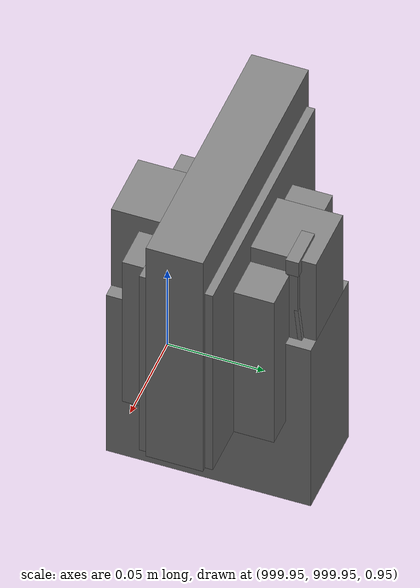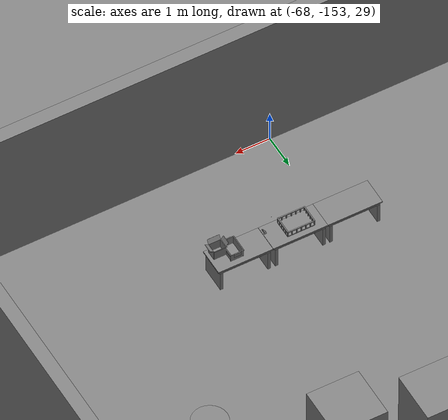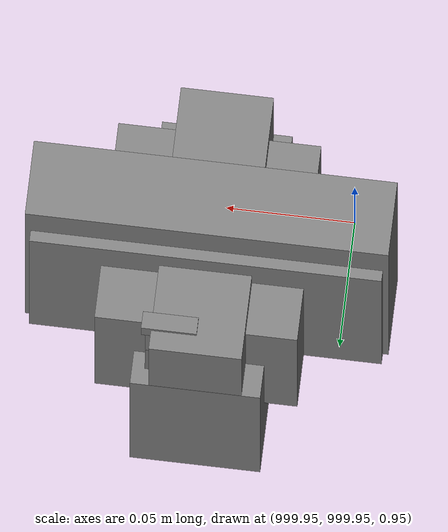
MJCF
<mujoco>
    <option gravity="0.000000000 0.000000000 -9.810000420" timestep="0.0049999999" integrator="implicitfast" density="1.225" viscosity="1.8000001e-05" noslip_iterations="10" iterations="100" sdf_iterations="50">
        <flag multiccd="disable"/>
    </option>
    <size memory="1000M"/>
    <compiler coordinate="local"/>
    <worldbody>
        <light cutoff="30" pos="0 1 1" dir="0 -1 -2"/>
        <light cutoff="30" pos="0 -1 1" dir="0 1 -2"/>
        <body pos="-64.866622925 -149.383972168 30.183746338" euler="89.999984741 89.999946594 0.000000000" name="openloong_gripper_2f85_fix_base_usda_bluebox_01">
            <geom contype="1" conaffinity="1" density="1000" type="box" material="" rgba="0.500000000 0.500000000 0.500000000 1.000000000" solimp="0.899999976 0.949999988 0.001000000" friction="1.000000000 0.005000000 0.000100000" solref="0.020000000 1.000000000" margin="0" condim="3" group="0" pos="0.276580811 0.187225342 0.000068665" quat="0.707106948 0.000077471 0.707106352 0.000077486" size="0.100000001 0.057999998 0.010000000" name="openloong_gripper_2f85_fix_base_usda_geom_EADC4376_A79C_467D_B88A_4433B1A0569B"/>
            <geom contype="1" conaffinity="1" density="1000" type="box" material="" rgba="0.500000000 0.500000000 0.500000000 1.000000000" solimp="0.899999976 0.949999988 0.001000000" friction="1.000000000 0.005000000 0.000100000" solref="0.020000000 1.000000000" margin="0" condim="3" group="0" pos="0.000000000 0.002883911 0.000000000" quat="0.999999881 0.000000000 0.000000000 0.000000000" size="0.254000008 0.003000000 0.172000006" name="openloong_gripper_2f85_fix_base_usda_geom_F06DEC08_3749_4492_A8D1_FD43D6B0BD0A"/>
            <geom contype="1" conaffinity="1" density="1000" type="box" material="" rgba="0.500000000 0.500000000 0.500000000 1.000000000" solimp="0.899999976 0.949999988 0.001000000" friction="1.000000000 0.005000000 0.000100000" solref="0.020000000 1.000000000" margin="0" condim="3" group="0" pos="0.000000000 0.124874115 0.173484802" quat="0.999796331 0.020176515 -0.000000015 0.000000030" size="0.259999990 0.119999997 0.007000000" name="openloong_gripper_2f85_fix_base_usda_geom_E4C5F80E_79C6_4770_A3DE_F2156BE51797"/>
            <geom contype="1" conaffinity="1" density="1000" type="box" material="" rgba="0.500000000 0.500000000 0.500000000 1.000000000" solimp="0.899999976 0.949999988 0.001000000" friction="1.000000000 0.005000000 0.000100000" solref="0.020000000 1.000000000" margin="0" condim="3" group="0" pos="0.000000000 0.124874115 -0.173469543" quat="0.999796331 -0.020176545 -0.000000015 0.000000000" size="0.259999990 0.119999997 0.007000000" name="openloong_gripper_2f85_fix_base_usda_geom_ED7A2937_E71F_4EDB_BEF1_0F150F0B3332"/>
            <geom contype="1" conaffinity="1" density="1000" type="box" material="" rgba="0.500000000 0.500000000 0.500000000 1.000000000" solimp="0.899999976 0.949999988 0.001000000" friction="1.000000000 0.005000000 0.000100000" solref="0.020000000 1.000000000" margin="0" condim="3" group="0" pos="0.000000000 0.214008331 0.188980103" quat="0.999912977 0.013176724 0.000000015 0.000000000" size="0.259999990 0.029999999 0.012500000" name="openloong_gripper_2f85_fix_base_usda_geom_A1D35AFC_61AA_4FC2_80CE_574D9941B485"/>
            <geom contype="1" conaffinity="1" density="1000" type="box" material="" rgba="0.500000000 0.500000000 0.500000000 1.000000000" solimp="0.899999976 0.949999988 0.001000000" friction="1.000000000 0.005000000 0.000100000" solref="0.020000000 1.000000000" margin="0" condim="3" group="0" pos="-0.258361816 0.125289917 0.001876831" quat="0.702796936 -0.020792112 0.710783124 0.020769298" size="0.189999998 0.119999997 0.009000000" name="openloong_gripper_2f85_fix_base_usda_geom_D6342FC2_0AF6_4341_B887_27C112B52A10"/>
            <geom contype="1" conaffinity="1" density="1000" type="box" material="" rgba="0.500000000 0.500000000 0.500000000 1.000000000" solimp="0.899999976 0.949999988 0.001000000" friction="1.000000000 0.005000000 0.000100000" solref="0.020000000 1.000000000" margin="0" condim="3" group="0" pos="0.000000000 0.214008331 -0.188980103" quat="0.999912977 -0.013176769 0.000000030 0.000000015" size="0.259999990 0.029999999 0.012500000" name="openloong_gripper_2f85_fix_base_usda_geom_F3A7F49C_FFC5_4BF8_A75F_2439D17AD176"/>
            <geom contype="1" conaffinity="1" density="1000" type="box" material="" rgba="0.500000000 0.500000000 0.500000000 1.000000000" solimp="0.899999976 0.949999988 0.001000000" friction="1.000000000 0.005000000 0.000100000" solref="0.020000000 1.000000000" margin="0" condim="3" group="0" pos="-0.276611328 0.187225342 0.000068665" quat="0.707106650 0.000077441 0.707106709 0.000077456" size="0.100000001 0.057999998 0.010000000" name="openloong_gripper_2f85_fix_base_usda_geom_1DFC4714_2588_46FD_AED6_7481421ADEA2"/>
            <geom contype="1" conaffinity="1" density="1000" type="box" material="" rgba="0.500000000 0.500000000 0.500000000 1.000000000" solimp="0.899999976 0.949999988 0.001000000" friction="1.000000000 0.005000000 0.000100000" solref="0.020000000 1.000000000" margin="0" condim="3" group="0" pos="0.258331299 0.125289917 0.001876831" quat="0.702851415 0.018856421 0.710823774 -0.019329369" size="0.189999998 0.119999997 0.009000000" name="openloong_gripper_2f85_fix_base_usda_geom_BEFD5806_7268_4395_BF87_CCDE892CB038"/>
            <freejoint name="openloong_gripper_2f85_fix_base_usda_bluebox_01_joint"/>
            <site size="0.005000000 0.005000000 0.005000000" rgba="0.500000000 0.500000000 0.500000000 1.000000000" pos="0.000000000 0.000000000 0.000000000" quat="0.999961913 0.008726534 0.000000000 0.000000000" group="0" type="sphere" name="openloong_gripper_2f85_fix_base_usda_bluebox_01site"/>
        </body>
        <body pos="-64.496299744 -149.491867065 30.235729218" euler="0.000000000 0.000000000 89.999946594" name="openloong_gripper_2f85_fix_base_usda_cardboardbox_01">
            <geom contype="1" conaffinity="1" density="1000" type="box" material="" rgba="0.500000000 0.500000000 0.500000000 1.000000000" solimp="0.899999976 0.949999988 0.001000000" friction="1.000000000 0.005000000 0.000100000" solref="0.020000000 1.000000000" margin="0" condim="3" group="0" pos="-0.003166199 -0.004086494 0.005052090" quat="1.000000000 0.000000000 0.000000000 0.000000000" size="0.142499998 0.177500010 0.005000000" name="openloong_gripper_2f85_fix_base_usda_geom_488C919B_F746_442F_B216_76B49235E2F8"/>
            <geom contype="1" conaffinity="1" density="1000" type="box" material="" rgba="0.500000000 0.500000000 0.500000000 1.000000000" solimp="0.899999976 0.949999988 0.001000000" friction="1.000000000 0.005000000 0.000100000" solref="0.020000000 1.000000000" margin="0" condim="3" group="0" pos="-0.003166199 0.170316696 0.150570869" quat="1.000000000 0.000000000 0.000000000 0.000000000" size="0.142499998 0.005000000 0.149999991" name="openloong_gripper_2f85_fix_base_usda_geom_02DCEE19_F038_4E4B_B8E4_38DD154B6366"/>
            <geom contype="1" conaffinity="1" density="1000" type="box" material="" rgba="0.500000000 0.500000000 0.500000000 1.000000000" solimp="0.899999976 0.949999988 0.001000000" friction="1.000000000 0.005000000 0.000100000" solref="0.020000000 1.000000000" margin="0" condim="3" group="0" pos="-0.147399902 -0.005307198 0.150570869" quat="1.000000000 0.000000000 0.000000000 0.000000000" size="0.005000000 0.177500010 0.149999991" name="openloong_gripper_2f85_fix_base_usda_geom_5A1F2CAA_5930_42EC_8805_4FFB43679A53"/>
            <geom contype="1" conaffinity="1" density="1000" type="box" material="" rgba="0.500000000 0.500000000 0.500000000 1.000000000" solimp="0.899999976 0.949999988 0.001000000" friction="1.000000000 0.005000000 0.000100000" solref="0.020000000 1.000000000" margin="0" condim="3" group="0" pos="0.140275955 -0.005307198 0.150570869" quat="1.000000000 0.000000000 0.000000000 0.000000000" size="0.005000000 0.177500010 0.149999991" name="openloong_gripper_2f85_fix_base_usda_geom_2289C063_0D3A_4FED_8930_2054BE8075CC"/>
            <geom contype="1" conaffinity="1" density="1000" type="box" material="" rgba="0.500000000 0.500000000 0.500000000 1.000000000" solimp="0.899999976 0.949999988 0.001000000" friction="1.000000000 0.005000000 0.000100000" solref="0.020000000 1.000000000" margin="0" condim="3" group="0" pos="-0.003166199 -0.181550980 0.150570869" quat="1.000000000 0.000000000 0.000000000 0.000000000" size="0.142499998 0.005000000 0.149999991" name="openloong_gripper_2f85_fix_base_usda_geom_AB5F6C39_084C_4EBC_9326_B7465FF5190F"/>
            <freejoint name="openloong_gripper_2f85_fix_base_usda_cardboardbox_01_joint"/>
            <site size="0.005000000 0.005000000 0.005000000" rgba="0.500000000 0.500000000 0.500000000 1.000000000" pos="0.000000000 0.000000000 0.000000000" quat="0.999961913 0.008726535 0.000000000 0.000000000" group="0" type="sphere" name="openloong_gripper_2f85_fix_base_usda_site_6A605542_0FEB_484D_AE13_32FD9654DC48"/>
            <body pos="0.139160156 -0.004048347 0.301930904" euler="-179.999954224 49.383502960 179.999954224" name="openloong_gripper_2f85_fix_base_usda_A1_006">
                <geom contype="1" conaffinity="1" density="1000" type="box" material="" rgba="0.500000000 0.500000000 0.500000000 1.000000000" solimp="0.899999976 0.949999988 0.001000000" friction="1.000000000 0.005000000 0.000100000" solref="0.020000000 1.000000000" margin="0" condim="3" group="0" pos="-0.071587563 0.000009537 0.001745224" quat="0.999999881 0.000000000 0.000000000 0.000000000" size="0.071249999 0.179999992 0.002500000" name="openloong_gripper_2f85_fix_base_usda_geom_1192FC53_C2B0_4CBF_A1B2_ACAD8D5372FF"/>
                <joint armature="0" stiffness="0.07" damping="0.0099999998" axis="0.000000 1.000000 0.000000" type="hinge" name="openloong_gripper_2f85_fix_base_usda_A1_006"/>
            </body>
            <body pos="-0.145902634 -0.004086494 0.301938057" euler="-180.000000000 -60.000011444 -180.000000000" name="openloong_gripper_2f85_fix_base_usda_A2_006">
                <geom contype="1" conaffinity="1" density="1000" type="box" material="" rgba="0.500000000 0.500000000 0.500000000 1.000000000" solimp="0.899999976 0.949999988 0.001000000" friction="1.000000000 0.005000000 0.000100000" solref="0.020000000 1.000000000" margin="0" condim="3" group="0" pos="0.071268082 0.000009537 0.002717972" quat="0.000002921 0.000000000 -0.000000030 0.999999881" size="0.071249999 0.179999992 0.002500000" name="openloong_gripper_2f85_fix_base_usda_geom_C9DBDA5F_EAC8_4502_9791_CB60B9663E33"/>
                <joint armature="0" stiffness="0.07" damping="0.0099999998" axis="0.000000 1.000000 0.000000" type="hinge" name="openloong_gripper_2f85_fix_base_usda_A2_006"/>
            </body>
            <body pos="-0.003385544 0.175991058 0.301930904" euler="-125.858116150 -0.000004561 0.000002331" name="openloong_gripper_2f85_fix_base_usda_B2_006">
                <geom contype="1" conaffinity="1" density="1000" type="box" material="" rgba="0.500000000 0.500000000 0.500000000 1.000000000" solimp="0.899999976 0.949999988 0.001000000" friction="1.000000000 0.005000000 0.000100000" solref="0.020000000 1.000000000" margin="0" condim="3" group="0" pos="0.000009537 -0.070939064 -0.002470016" quat="0.999614120 0.027776197 -0.000000015 0.000000030" size="0.137500003 0.064999998 0.005000000" name="openloong_gripper_2f85_fix_base_usda_geom_F28B5615_3461_4578_8BC5_3AE8E76DE13B"/>
                <joint armature="0" stiffness="0.07" damping="0.0099999998" axis="1.000000 0.000000 0.000000" type="hinge" name="openloong_gripper_2f85_fix_base_usda_B2_006"/>
            </body>
            <body pos="-0.003385544 -0.184140205 0.301938057" euler="147.805557251 0.000000000 0.000000000" name="openloong_gripper_2f85_fix_base_usda_B1_006">
                <geom contype="1" conaffinity="1" density="1000" type="box" material="" rgba="0.500000000 0.500000000 0.500000000 1.000000000" solimp="0.899999976 0.949999988 0.001000000" friction="1.000000000 0.005000000 0.000100000" solref="0.020000000 1.000000000" margin="0" condim="3" group="0" pos="-0.000028610 0.070202351 -0.002703667" quat="0.999614179 -0.027776167 0.000000000 0.000000000" size="0.137500003 0.064999998 0.005000000" name="openloong_gripper_2f85_fix_base_usda_geom_3850BE0E_1356_4F61_963D_F28B4003BB88"/>
                <joint armature="0" stiffness="0.07" damping="0.0099999998" axis="1.000000 0.000000 0.000000" type="hinge" name="openloong_gripper_2f85_fix_base_usda_B1_006"/>
            </body>
        </body>
        <body pos="-65.882858276 -149.481979370 30.229999542" euler="-64.487716675 0.000000000 0.000000000" name="openloong_gripper_2f85_fix_base_usda_Barcode">
            <geom contype="1" conaffinity="1" density="1000" type="box" material="" rgba="0.500000000 0.500000000 0.500000000 1.000000000" solimp="0.899999976 0.949999988 0.001000000" friction="1.000000000 0.005000000 0.000100000" solref="0.020000000 1.000000000" margin="0" condim="3" group="0" pos="0.000000000 0.013038635 0.001419067" quat="0.000000000 0.000000000 0.000000000 1.000000119" size="0.034000002 0.010000000 0.017999999" name="openloong_gripper_2f85_fix_base_usda_geom_35BC2C42_1DC0_42D1_A01D_87B2D167255B"/>
            <geom contype="1" conaffinity="1" density="1000" type="box" material="" rgba="0.500000000 0.500000000 0.500000000 1.000000000" solimp="0.899999976 0.949999988 0.001000000" friction="1.000000000 0.005000000 0.000100000" solref="0.020000000 1.000000000" margin="0" condim="3" group="0" pos="0.000000000 -0.035301208 -0.007095337" quat="0.000000000 0.000000000 -0.043619365 0.999048233" size="0.028999999 0.010000000 0.020000000" name="openloong_gripper_2f85_fix_base_usda_geom_5E0D2D8F_9903_4348_A18D_7D5EDEB1B498"/>
            <geom contype="1" conaffinity="1" density="1000" type="box" material="" rgba="0.500000000 0.500000000 0.500000000 1.000000000" solimp="0.899999976 0.949999988 0.001000000" friction="1.000000000 0.005000000 0.000100000" solref="0.020000000 1.000000000" margin="0" condim="3" group="0" pos="0.000000000 -0.043411255 -0.011749268" quat="0.922262907 0.386563420 0.000000000 0.000000000" size="0.026000001 0.010000000 0.020000000" name="openloong_gripper_2f85_fix_base_usda_geom_C7912011_379A_4048_86E1_1815E3B58E3C"/>
            <geom contype="1" conaffinity="1" density="1000" type="box" material="" rgba="0.500000000 0.500000000 0.500000000 1.000000000" solimp="0.899999976 0.949999988 0.001000000" friction="1.000000000 0.005000000 0.000100000" solref="0.020000000 1.000000000" margin="0" condim="3" group="0" pos="0.000000000 -0.016967773 -0.031860352" quat="0.000000000 0.000000000 0.000000000 1.000000119" size="0.008000000 0.010000000 0.013000000" name="openloong_gripper_2f85_fix_base_usda_geom_240665FF_056C_42BE_8544_AF76C24EA0DC"/>
            <geom contype="1" conaffinity="1" density="1000" type="box" material="" rgba="0.500000000 0.500000000 0.500000000 1.000000000" solimp="0.899999976 0.949999988 0.001000000" friction="1.000000000 0.005000000 0.000100000" solref="0.020000000 1.000000000" margin="0" condim="3" group="0" pos="0.000000000 -0.001869202 0.000312805" quat="0.953716993 0.300705761 0.000000000 0.000000000" size="0.032000002 0.010000000 0.018999999" name="openloong_gripper_2f85_fix_base_usda_geom_6AD51681_53F7_463F_B4F2_CAA1B606BFB2"/>
            <geom contype="1" conaffinity="1" density="1000" type="box" material="" rgba="0.500000000 0.500000000 0.500000000 1.000000000" solimp="0.899999976 0.949999988 0.001000000" friction="1.000000000 0.005000000 0.000100000" solref="0.020000000 1.000000000" margin="0" condim="3" group="0" pos="0.000000000 -0.019531250 -0.003173828" quat="0.953716993 0.300705761 0.000000000 0.000000000" size="0.030999999 0.010000000 0.020000000" name="openloong_gripper_2f85_fix_base_usda_geom_9C538611_C73B_4D1B_8600_80B029A6F167"/>
            <geom contype="1" conaffinity="1" density="1000" type="box" material="" rgba="0.500000000 0.500000000 0.500000000 1.000000000" solimp="0.899999976 0.949999988 0.001000000" friction="1.000000000 0.005000000 0.000100000" solref="0.020000000 1.000000000" margin="0" condim="3" group="0" pos="0.000000000 -0.035301208 -0.007095337" quat="0.953716993 0.300705761 0.000000000 0.000000000" size="0.028999999 0.010000000 0.020000000" name="openloong_gripper_2f85_fix_base_usda_geom_95955E5F_FA5F_4D3F_A97D_A41558B90A8C"/>
            <geom contype="1" conaffinity="1" density="1000" type="box" material="" rgba="0.500000000 0.500000000 0.500000000 1.000000000" solimp="0.899999976 0.949999988 0.001000000" friction="1.000000000 0.005000000 0.000100000" solref="0.020000000 1.000000000" margin="0" condim="3" group="0" pos="0.000000000 -0.042617798 -0.071121216" quat="0.000000000 0.000000000 0.000000000 1.000000119" size="0.013000000 0.021000000 0.059999999" name="openloong_gripper_2f85_fix_base_usda_geom_8ECDFF43_8EAA_439E_852C_60D0EFB86E6B"/>
            <freejoint name="openloong_gripper_2f85_fix_base_usda_Barcode_joint"/>
            <site size="0.005000000 0.005000000 0.005000000" rgba="0.500000000 0.500000000 0.500000000 1.000000000" pos="0.000000000 0.000000000 0.000000000" quat="1.000000000 0.000000000 0.000000000 0.000000000" group="0" type="sphere" name="openloong_gripper_2f85_fix_base_usda_Barcode_site"/>
        </body>
        <body pos="-66.745018005 -149.392349243 30.184000015" euler="0.000000000 0.000000000 89.999946594" name="[22332657348189]_Basket_01">
            <geom contype="1" conaffinity="1" density="1000" type="box" material="" rgba="0.500000000 0.500000000 0.500000000 1.000000000" solimp="0.899999976 0.949999988 0.001000000" friction="1.000000000 0.005000000 0.000100000" solref="0.020000000 1.000000000" margin="0" condim="3" group="0" pos="-0.052425385 0.389207840 0.089787483" quat="0.707107008 0.000000000 0.000000000 0.707106411" size="0.014249999 0.014249999 0.059999999" name="[22332657348189]_geom_B6864BF5_58F4_41BC_9127_8C2A934B8772"/>
            <geom contype="1" conaffinity="1" density="1000" type="box" material="" rgba="0.500000000 0.500000000 0.500000000 1.000000000" solimp="0.899999976 0.949999988 0.001000000" friction="1.000000000 0.005000000 0.000100000" solref="0.020000000 1.000000000" margin="0" condim="3" group="0" pos="0.264015198 -0.133043289 0.089787483" quat="0.707107008 0.000000000 0.000000000 0.707106411" size="0.014249999 0.014249999 0.059999999" name="[22332657348189]_geom_9E237660_4EDF_4637_ABD3_AAE4794085E5"/>
            <geom contype="1" conaffinity="1" density="1000" type="box" material="" rgba="0.500000000 0.500000000 0.500000000 1.000000000" solimp="0.899999976 0.949999988 0.001000000" friction="1.000000000 0.005000000 0.000100000" solref="0.020000000 1.000000000" margin="0" condim="3" group="0" pos="-0.264015198 -0.265548706 0.089793205" quat="0.707107008 0.000000000 0.000000000 0.707106411" size="0.014249999 0.014249999 0.059999999" name="[22332657348189]_geom_7C149114_C94E_48AD_A352_2BBD5F250E8F"/>
            <geom contype="1" conaffinity="1" density="1000" type="box" material="" rgba="0.500000000 0.500000000 0.500000000 1.000000000" solimp="0.899999976 0.949999988 0.001000000" friction="1.000000000 0.005000000 0.000100000" solref="0.020000000 1.000000000" margin="0" condim="3" group="0" pos="-0.160263062 -0.389322281 0.089793205" quat="0.707107008 0.000000000 0.000000000 0.707106411" size="0.014249999 0.014249999 0.059999999" name="[22332657348189]_geom_F0FC8DFE_E435_4501_B5E5_4B1DE1AA1FB2"/>
            <geom contype="1" conaffinity="1" density="1000" type="box" material="" rgba="0.500000000 0.500000000 0.500000000 1.000000000" solimp="0.899999976 0.949999988 0.001000000" friction="1.000000000 0.005000000 0.000100000" solref="0.020000000 1.000000000" margin="0" condim="3" group="0" pos="0.162265778 -0.389322281 0.089787483" quat="0.707107008 0.000000000 0.000000000 0.707106411" size="0.014249999 0.014249999 0.059999999" name="[22332657348189]_geom_21DE14AB_B558_428D_B54A_38CAFB2D6AD4"/>
            <geom contype="1" conaffinity="1" density="1000" type="box" material="" rgba="0.500000000 0.500000000 0.500000000 1.000000000" solimp="0.899999976 0.949999988 0.001000000" friction="1.000000000 0.005000000 0.000100000" solref="0.020000000 1.000000000" margin="0" condim="3" group="0" pos="0.264015198 0.389207840 0.089787483" quat="0.707107008 0.000000000 0.000000000 0.707106411" size="0.014249999 0.014249999 0.059999999" name="[22332657348189]_geom_402F6C3E_AF62_4131_808C_0BD0291BB993"/>
            <geom contype="1" conaffinity="1" density="1000" type="box" material="" rgba="0.500000000 0.500000000 0.500000000 1.000000000" solimp="0.899999976 0.949999988 0.001000000" friction="1.000000000 0.005000000 0.000100000" solref="0.020000000 1.000000000" margin="0" condim="3" group="0" pos="-0.264015198 -0.133043289 0.089793205" quat="0.707107008 0.000000000 0.000000000 0.707106411" size="0.014249999 0.014249999 0.059999999" name="[22332657348189]_geom_BAB48FBD_43AD_4FA6_BD54_CC728A6ED866"/>
            <geom contype="1" conaffinity="1" density="1000" type="box" material="" rgba="0.500000000 0.500000000 0.500000000 1.000000000" solimp="0.899999976 0.949999988 0.001000000" friction="1.000000000 0.005000000 0.000100000" solref="0.020000000 1.000000000" margin="0" condim="3" group="0" pos="-0.264026642 0.269256592 0.089793205" quat="0.707107008 0.000000000 0.000000000 0.707106411" size="0.014249999 0.014249999 0.059999999" name="[22332657348189]_geom_A2D4CDFF_31D7_40B5_874D_05D08ABA2B06"/>
            <geom contype="1" conaffinity="1" density="1000" type="box" material="" rgba="0.500000000 0.500000000 0.500000000 1.000000000" solimp="0.899999976 0.949999988 0.001000000" friction="1.000000000 0.005000000 0.000100000" solref="0.020000000 1.000000000" margin="0" condim="3" group="0" pos="0.054462433 0.389207840 0.089787483" quat="0.707107008 0.000000000 0.000000000 0.707106411" size="0.014249999 0.014249999 0.059999999" name="[22332657348189]_geom_74F7590B_ADCD_4F2D_978E_8C22315BC2D7"/>
            <geom contype="1" conaffinity="1" density="1000" type="box" material="" rgba="0.500000000 0.500000000 0.500000000 1.000000000" solimp="0.899999976 0.949999988 0.001000000" friction="1.000000000 0.005000000 0.000100000" solref="0.020000000 1.000000000" margin="0" condim="3" group="0" pos="0.054462433 -0.389322281 0.089787483" quat="0.707107008 0.000000000 0.000000000 0.707106411" size="0.014249999 0.014249999 0.059999999" name="[22332657348189]_geom_1BD6C35A_A574_418B_8BCD_52BF9B5D9E1A"/>
            <geom contype="1" conaffinity="1" density="1000" type="box" material="" rgba="0.500000000 0.500000000 0.500000000 1.000000000" solimp="0.899999976 0.949999988 0.001000000" friction="1.000000000 0.005000000 0.000100000" solref="0.020000000 1.000000000" margin="0" condim="3" group="0" pos="0.264015198 0.269256592 0.089793205" quat="0.707107008 0.000000000 0.000000000 0.707106411" size="0.014249999 0.014249999 0.059999999" name="[22332657348189]_geom_62C7C503_59F8_4A78_8DC5_885E9FF68C39"/>
            <geom contype="1" conaffinity="1" density="1000" type="box" material="" rgba="0.500000000 0.500000000 0.500000000 1.000000000" solimp="0.899999976 0.949999988 0.001000000" friction="1.000000000 0.005000000 0.000100000" solref="0.020000000 1.000000000" margin="0" condim="3" group="0" pos="0.264015198 -0.389322281 0.089787483" quat="0.707107008 0.000000000 0.000000000 0.707106411" size="0.014249999 0.014249999 0.059999999" name="[22332657348189]_geom_E2E83519_0320_458D_A419_D885AD383AA4"/>
            <geom contype="1" conaffinity="1" density="1000" type="box" material="" rgba="0.500000000 0.500000000 0.500000000 1.000000000" solimp="0.899999976 0.949999988 0.001000000" friction="1.000000000 0.005000000 0.000100000" solref="0.020000000 1.000000000" margin="0" condim="3" group="0" pos="0.000000000 0.000000000 0.015998840" quat="0.707107008 0.000000000 0.000000000 0.707106411" size="0.403499991 0.279000014 0.015750000" name="[22332657348189]_geom_47D5859C_B1FD_4FA6_9075_8AC21BA87DD6"/>
            <geom contype="1" conaffinity="1" density="1000" type="box" material="" rgba="0.500000000 0.500000000 0.500000000 1.000000000" solimp="0.899999976 0.949999988 0.001000000" friction="1.000000000 0.005000000 0.000100000" solref="0.020000000 1.000000000" margin="0" condim="3" group="0" pos="0.000000000 -0.389476776 0.163619041" quat="0.707107008 0.000000000 0.000000000 0.707106411" size="0.015000000 0.277500004 0.015750000" name="[22332657348189]_geom_2EE84D6E_E4FC_4FF1_A786_9246953CD86E"/>
            <geom contype="1" conaffinity="1" density="1000" type="box" material="" rgba="0.500000000 0.500000000 0.500000000 1.000000000" solimp="0.899999976 0.949999988 0.001000000" friction="1.000000000 0.005000000 0.000100000" solref="0.020000000 1.000000000" margin="0" condim="3" group="0" pos="0.162265778 0.389207840 0.089787483" quat="0.707107008 0.000000000 0.000000000 0.707106411" size="0.014249999 0.014249999 0.059999999" name="[22332657348189]_geom_38DC1453_1E60_47F7_A012_9DAF98AD6494"/>
            <geom contype="1" conaffinity="1" density="1000" type="box" material="" rgba="0.500000000 0.500000000 0.500000000 1.000000000" solimp="0.899999976 0.949999988 0.001000000" friction="1.000000000 0.005000000 0.000100000" solref="0.020000000 1.000000000" margin="0" condim="3" group="0" pos="0.000000000 0.389471054 0.163619041" quat="0.707107008 0.000000000 0.000000000 0.707106411" size="0.015000000 0.277500004 0.015750000" name="[22332657348189]_geom_7EB2C268_438B_4D66_9344_BD9485F5E8A8"/>
            <geom contype="1" conaffinity="1" density="1000" type="box" material="" rgba="0.500000000 0.500000000 0.500000000 1.000000000" solimp="0.899999976 0.949999988 0.001000000" friction="1.000000000 0.005000000 0.000100000" solref="0.020000000 1.000000000" margin="0" condim="3" group="0" pos="-0.263511658 0.000000000 0.163619041" quat="0.707107008 0.000000000 0.000000000 0.707106411" size="0.403499991 0.015000000 0.015750000" name="[22332657348189]_geom_E27E2D97_8780_4039_B0EB_F510CD57D3EE"/>
            <geom contype="1" conaffinity="1" density="1000" type="box" material="" rgba="0.500000000 0.500000000 0.500000000 1.000000000" solimp="0.899999976 0.949999988 0.001000000" friction="1.000000000 0.005000000 0.000100000" solref="0.020000000 1.000000000" margin="0" condim="3" group="0" pos="-0.264015198 0.141334534 0.089793205" quat="0.707107008 0.000000000 0.000000000 0.707106411" size="0.014249999 0.014249999 0.059999999" name="[22332657348189]_geom_C8385667_1930_4F2E_B22C_BCF5A45E5FE7"/>
            <geom contype="1" conaffinity="1" density="1000" type="box" material="" rgba="0.500000000 0.500000000 0.500000000 1.000000000" solimp="0.899999976 0.949999988 0.001000000" friction="1.000000000 0.005000000 0.000100000" solref="0.020000000 1.000000000" margin="0" condim="3" group="0" pos="0.264015198 -0.265548706 0.089787483" quat="0.707107008 0.000000000 0.000000000 0.707106411" size="0.014249999 0.014249999 0.059999999" name="[22332657348189]_geom_F44DE1D3_9CEE_485C_8BE8_51BC225A8BBE"/>
            <geom contype="1" conaffinity="1" density="1000" type="box" material="" rgba="0.500000000 0.500000000 0.500000000 1.000000000" solimp="0.899999976 0.949999988 0.001000000" friction="1.000000000 0.005000000 0.000100000" solref="0.020000000 1.000000000" margin="0" condim="3" group="0" pos="-0.160263062 0.389207840 0.089787483" quat="0.707107008 0.000000000 0.000000000 0.707106411" size="0.014249999 0.014249999 0.059999999" name="[22332657348189]_geom_A2BC397C_95A1_466B_BDA2_0C129425F006"/>
            <geom contype="1" conaffinity="1" density="1000" type="box" material="" rgba="0.500000000 0.500000000 0.500000000 1.000000000" solimp="0.899999976 0.949999988 0.001000000" friction="1.000000000 0.005000000 0.000100000" solref="0.020000000 1.000000000" margin="0" condim="3" group="0" pos="-0.052425385 -0.389322281 0.089787483" quat="0.707107008 0.000000000 0.000000000 0.707106411" size="0.014249999 0.014249999 0.059999999" name="[22332657348189]_geom_0F369F53_D015_48E4_B747_61F789D5640E"/>
            <geom contype="1" conaffinity="1" density="1000" type="box" material="" rgba="0.500000000 0.500000000 0.500000000 1.000000000" solimp="0.899999976 0.949999988 0.001000000" friction="1.000000000 0.005000000 0.000100000" solref="0.020000000 1.000000000" margin="0" condim="3" group="0" pos="-0.264026642 -0.389322281 0.089793205" quat="0.707107008 0.000000000 0.000000000 0.707106411" size="0.014249999 0.014249999 0.059999999" name="[22332657348189]_geom_56FB6393_4E81_45BC_8122_8A22C65D36FA"/>
            <geom contype="1" conaffinity="1" density="1000" type="box" material="" rgba="0.500000000 0.500000000 0.500000000 1.000000000" solimp="0.899999976 0.949999988 0.001000000" friction="1.000000000 0.005000000 0.000100000" solref="0.020000000 1.000000000" margin="0" condim="3" group="0" pos="0.264015198 0.141334534 0.089787483" quat="0.707107008 0.000000000 0.000000000 0.707106411" size="0.014249999 0.014249999 0.059999999" name="[22332657348189]_geom_709939D6_FA66_43DE_AE19_24AE20F65FF9"/>
            <geom contype="1" conaffinity="1" density="1000" type="box" material="" rgba="0.500000000 0.500000000 0.500000000 1.000000000" solimp="0.899999976 0.949999988 0.001000000" friction="1.000000000 0.005000000 0.000100000" solref="0.020000000 1.000000000" margin="0" condim="3" group="0" pos="-0.264015198 0.389207840 0.089793205" quat="0.707107008 0.000000000 0.000000000 0.707106411" size="0.014249999 0.014249999 0.059999999" name="[22332657348189]_geom_A2F28FDA_073F_4C46_9B86_3EBBC1D8E685"/>
            <geom contype="1" conaffinity="1" density="1000" type="box" material="" rgba="0.500000000 0.500000000 0.500000000 1.000000000" solimp="0.899999976 0.949999988 0.001000000" friction="1.000000000 0.005000000 0.000100000" solref="0.020000000 1.000000000" margin="0" condim="3" group="0" pos="0.264015198 0.004480362 0.089787483" quat="0.707107008 0.000000000 0.000000000 0.707106411" size="0.014249999 0.014249999 0.059999999" name="[22332657348189]_geom_01ED9EEA_7A92_479B_8ED0_CBF374E0981A"/>
            <geom contype="1" conaffinity="1" density="1000" type="box" material="" rgba="0.500000000 0.500000000 0.500000000 1.000000000" solimp="0.899999976 0.949999988 0.001000000" friction="1.000000000 0.005000000 0.000100000" solref="0.020000000 1.000000000" margin="0" condim="3" group="0" pos="0.263694763 -0.000011444 0.163619041" quat="0.707107008 0.000000000 0.000000000 0.707106411" size="0.403499991 0.015000000 0.015750000" name="[22332657348189]_geom_997A2B82_E277_424D_8D34_D00B84BC4B6C"/>
            <geom contype="1" conaffinity="1" density="1000" type="box" material="" rgba="0.500000000 0.500000000 0.500000000 1.000000000" solimp="0.899999976 0.949999988 0.001000000" friction="1.000000000 0.005000000 0.000100000" solref="0.020000000 1.000000000" margin="0" condim="3" group="0" pos="-0.264015198 0.004480362 0.089793205" quat="0.707107008 0.000000000 0.000000000 0.707106411" size="0.014249999 0.014249999 0.059999999" name="[22332657348189]_geom_CD33FBFB_5D6A_4F90_8256_29216EB42E6B"/>
            <freejoint name="[22332657348189]_joint_03D5B061_BA1A_4A04_8B2E_66E113691CBC"/>
        </body>
        <body pos="0.000000000 0.000000000 0.000000000" euler="0.000000000 0.000000000 0.000000000" name="Static Objects_Static Objects">
            <geom contype="1" conaffinity="1" density="1000" type="box" material="" rgba="0.500000000 0.500000000 0.500000000 1.000000000" solimp="0.899999976 0.949999988 0.001000000" friction="1.000000000 0.005000000 0.000100000" solref="0.020000000 1.000000000" margin="0" condim="3" group="0" pos="-67.544113159 -149.365814209 29.727830887" quat="0.500000417 0.499999970 0.499999553 0.499999970" size="0.381000012 0.319999993 0.041000001" name="Static Objects_geom_6EF3642A_FDF4_418A_BEFE_7CEB8E6EFEE6"/>
            <geom contype="1" conaffinity="1" density="1000" type="box" material="" rgba="0.500000000 0.500000000 0.500000000 1.000000000" solimp="0.899999976 0.949999988 0.001000000" friction="1.000000000 0.005000000 0.000100000" solref="0.020000000 1.000000000" margin="0" condim="3" group="0" pos="-68.239501953 -149.365814209 30.086868286" quat="0.500000417 0.499999970 0.499999553 0.499999970" size="0.370999992 0.039500002 0.745000005" name="Static Objects_geom_DBED85BB_A23F_45A5_9A9C_7D86E5FE0B41"/>
            <geom contype="1" conaffinity="1" density="1000" type="box" material="" rgba="0.500000000 0.500000000 0.500000000 1.000000000" solimp="0.899999976 0.949999988 0.001000000" friction="1.000000000 0.005000000 0.000100000" solref="0.020000000 1.000000000" margin="0" condim="3" group="0" pos="-68.239501953 -149.365814209 30.147235870" quat="0.500000417 0.499999970 0.499999553 0.499999970" size="0.400000006 0.022000000 0.800000012" name="Static Objects_geom_27338357_1591_40C3_BB78_18CF2531A9B1"/>
            <geom contype="1" conaffinity="1" density="1000" type="box" material="" rgba="0.500000000 0.500000000 0.500000000 1.000000000" solimp="0.899999976 0.949999988 0.001000000" friction="1.000000000 0.005000000 0.000100000" solref="0.020000000 1.000000000" margin="0" condim="3" group="0" pos="-68.934890747 -149.365814209 29.727830887" quat="0.500000417 0.499999970 0.499999553 0.499999970" size="0.381000012 0.319999993 0.041000001" name="Static Objects_geom_2836CE2F_DDAA_4E6A_A3BF_171EBC47515E"/>
            <geom contype="1" conaffinity="1" density="1000" type="box" material="" rgba="0.500000000 0.500000000 0.500000000 1.000000000" solimp="0.899999976 0.949999988 0.001000000" friction="1.000000000 0.005000000 0.000100000" solref="0.020000000 1.000000000" margin="0" condim="3" group="0" pos="-68.239501953 -149.365814209 29.561563492" quat="0.500000417 0.499999970 0.499999553 0.499999970" size="0.020000000 0.022000000 0.660000026" name="Static Objects_geom_AF94E2B3_A147_4170_8F06_CF55430C0587"/>
            <geom contype="1" conaffinity="1" density="1000" type="box" material="" rgba="0.500000000 0.500000000 0.500000000 1.000000000" solimp="0.899999976 0.949999988 0.001000000" friction="1.000000000 0.005000000 0.000100000" solref="0.020000000 1.000000000" margin="0" condim="3" group="0" pos="-65.945671082 -149.365814209 29.727830887" quat="0.500000417 0.499999970 0.499999553 0.499999970" size="0.381000012 0.319999993 0.041000001" name="Static Objects_geom_71A77B30_1799_4015_A8F8_C6D7D7B2CA5F"/>
            <geom contype="1" conaffinity="1" density="1000" type="box" material="" rgba="0.500000000 0.500000000 0.500000000 1.000000000" solimp="0.899999976 0.949999988 0.001000000" friction="1.000000000 0.005000000 0.000100000" solref="0.020000000 1.000000000" margin="0" condim="3" group="0" pos="-66.641059875 -149.365814209 30.086868286" quat="0.500000417 0.499999970 0.499999553 0.499999970" size="0.370999992 0.039500002 0.745000005" name="Static Objects_geom_59EEF1A8_19D6_4196_BFDD_50D3F5B24BB4"/>
            <geom contype="1" conaffinity="1" density="1000" type="box" material="" rgba="0.500000000 0.500000000 0.500000000 1.000000000" solimp="0.899999976 0.949999988 0.001000000" friction="1.000000000 0.005000000 0.000100000" solref="0.020000000 1.000000000" margin="0" condim="3" group="0" pos="-66.641059875 -149.365814209 30.147235870" quat="0.500000417 0.499999970 0.499999553 0.499999970" size="0.400000006 0.022000000 0.800000012" name="Static Objects_geom_AF2E6F4A_1283_41CA_BCA4_51455EB36A3B"/>
            <geom contype="1" conaffinity="1" density="1000" type="box" material="" rgba="0.500000000 0.500000000 0.500000000 1.000000000" solimp="0.899999976 0.949999988 0.001000000" friction="1.000000000 0.005000000 0.000100000" solref="0.020000000 1.000000000" margin="0" condim="3" group="0" pos="-67.336448669 -149.365814209 29.727830887" quat="0.500000417 0.499999970 0.499999553 0.499999970" size="0.381000012 0.319999993 0.041000001" name="Static Objects_geom_4E80E19F_86FB_4868_8634_789E9207151F"/>
            <geom contype="1" conaffinity="1" density="1000" type="box" material="" rgba="0.500000000 0.500000000 0.500000000 1.000000000" solimp="0.899999976 0.949999988 0.001000000" friction="1.000000000 0.005000000 0.000100000" solref="0.020000000 1.000000000" margin="0" condim="3" group="0" pos="-66.641059875 -149.365814209 29.561563492" quat="0.500000417 0.499999970 0.499999553 0.499999970" size="0.020000000 0.022000000 0.660000026" name="Static Objects_geom_FBF29564_7769_4ABE_9C38_B50BE851C2EB"/>
            <geom contype="1" conaffinity="1" density="1000" type="box" material="" rgba="0.500000000 0.500000000 0.500000000 1.000000000" solimp="0.899999976 0.949999988 0.001000000" friction="1.000000000 0.005000000 0.000100000" solref="0.020000000 1.000000000" margin="0" condim="3" group="0" pos="-64.338577271 -149.365814209 29.727830887" quat="0.500000417 0.499999970 0.499999553 0.499999970" size="0.381000012 0.319999993 0.041000001" name="Static Objects_geom_A71D92C1_5775_42B5_B4C2_C7249557B5E2"/>
            <geom contype="1" conaffinity="1" density="1000" type="box" material="" rgba="0.500000000 0.500000000 0.500000000 1.000000000" solimp="0.899999976 0.949999988 0.001000000" friction="1.000000000 0.005000000 0.000100000" solref="0.020000000 1.000000000" margin="0" condim="3" group="0" pos="-65.033966064 -149.365814209 30.086868286" quat="0.500000417 0.499999970 0.499999553 0.499999970" size="0.370999992 0.039500002 0.745000005" name="Static Objects_geom_9A1ECB6B_9168_4A83_9D94_DB20638E27E8"/>
            <geom contype="1" conaffinity="1" density="1000" type="box" material="" rgba="0.500000000 0.500000000 0.500000000 1.000000000" solimp="0.899999976 0.949999988 0.001000000" friction="1.000000000 0.005000000 0.000100000" solref="0.020000000 1.000000000" margin="0" condim="3" group="0" pos="-65.033966064 -149.365814209 30.147235870" quat="0.500000417 0.499999970 0.499999553 0.499999970" size="0.400000006 0.022000000 0.800000012" name="Static Objects_geom_1B4E814B_4CE8_4BD1_9196_C6C0E990D536"/>
            <geom contype="1" conaffinity="1" density="1000" type="box" material="" rgba="0.500000000 0.500000000 0.500000000 1.000000000" solimp="0.899999976 0.949999988 0.001000000" friction="1.000000000 0.005000000 0.000100000" solref="0.020000000 1.000000000" margin="0" condim="3" group="0" pos="-65.729354858 -149.365814209 29.727830887" quat="0.500000417 0.499999970 0.499999553 0.499999970" size="0.381000012 0.319999993 0.041000001" name="Static Objects_geom_4B4F938E_1738_4A47_B8BD_F8D895A48DBE"/>
            <geom contype="1" conaffinity="1" density="1000" type="box" material="" rgba="0.500000000 0.500000000 0.500000000 1.000000000" solimp="0.899999976 0.949999988 0.001000000" friction="1.000000000 0.005000000 0.000100000" solref="0.020000000 1.000000000" margin="0" condim="3" group="0" pos="-65.033966064 -149.365814209 29.561563492" quat="0.500000417 0.499999970 0.499999553 0.499999970" size="0.020000000 0.022000000 0.660000026" name="Static Objects_geom_02396205_7691_4F86_8DD2_25E95DDEC9B0"/>
            <geom contype="1" conaffinity="1" density="1000" type="box" material="" rgba="0.500000000 0.500000000 0.500000000 1.000000000" solimp="0.899999976 0.949999988 0.001000000" friction="1.000000000 0.005000000 0.000100000" solref="0.020000000 1.000000000" margin="0" condim="3" group="0" pos="-61.754566193 -137.853729248 33.906845093" quat="0.707107067 0.000000000 0.000000000 0.707106471" size="0.759999990 0.759999990 4.500000000" name="Static Objects_geom_D6B4C96F_DBAB_4C10_99E7_500BF18FE29C"/>
            <geom contype="1" conaffinity="1" density="1000" type="box" material="" rgba="0.500000000 0.500000000 0.500000000 1.000000000" solimp="0.899999976 0.949999988 0.001000000" friction="1.000000000 0.005000000 0.000100000" solref="0.020000000 1.000000000" margin="0" condim="3" group="0" pos="-57.511135101 -144.927108765 31.707921982" quat="1.000000000 0.000000000 0.000000000 0.000000000" size="0.200000003 8.000000000 2.299999952" name="Static Objects_geom_291E4BB1_8E26_4388_B673_777C3F6288C3"/>
            <geom contype="1" conaffinity="1" density="1000" type="box" material="" rgba="0.500000000 0.500000000 0.500000000 1.000000000" solimp="0.899999976 0.949999988 0.001000000" friction="1.000000000 0.005000000 0.000100000" solref="0.020000000 1.000000000" margin="0" condim="3" group="0" pos="-80.517646790 -157.574050903 31.688196182" quat="0.707107067 0.000000000 0.000000000 0.707106471" size="0.600000024 0.600000024 2.299999952" name="Static Objects_geom_B7C41455_10F9_4228_A5E0_3CEA0923E4D1"/>
            <geom contype="1" conaffinity="1" density="1000" type="box" material="" rgba="0.500000000 0.500000000 0.500000000 1.000000000" solimp="0.899999976 0.949999988 0.001000000" friction="1.000000000 0.005000000 0.000100000" solref="0.020000000 1.000000000" margin="0" condim="3" group="0" pos="-80.711044312 -147.414932251 31.666158676" quat="1.000000000 0.000000000 0.000000000 0.000000000" size="0.200000003 10.000000000 2.299999952" name="Static Objects_geom_4638AAD4_B090_4187_9A83_A83842C192C9"/>
            <geom contype="1" conaffinity="1" density="1000" type="box" material="" rgba="0.500000000 0.500000000 0.500000000 1.000000000" solimp="0.899999976 0.949999988 0.001000000" friction="1.000000000 0.005000000 0.000100000" solref="0.020000000 1.000000000" margin="0" condim="3" group="0" pos="-57.687217712 -137.434692383 31.688196182" quat="0.707107067 0.000000000 0.000000000 0.707106471" size="0.600000024 0.600000024 2.299999952" name="Static Objects_geom_46E4E4C2_A484_460F_ABC0_4F73050A5DA0"/>
            <geom contype="1" conaffinity="1" density="1000" type="box" material="" rgba="0.500000000 0.500000000 0.500000000 1.000000000" solimp="0.899999976 0.949999988 0.001000000" friction="1.000000000 0.005000000 0.000100000" solref="0.020000000 1.000000000" margin="0" condim="3" group="0" pos="-69.537033081 -140.263229370 31.714921951" quat="0.707107067 0.000000000 0.000000000 0.707106471" size="0.759999990 4.500000000 2.299999952" name="Static Objects_geom_3738BBFF_7898_4646_A58F_DDD737CF84DD"/>
            <geom contype="1" conaffinity="1" density="1000" type="box" material="" rgba="0.500000000 0.500000000 0.500000000 1.000000000" solimp="0.899999976 0.949999988 0.001000000" friction="1.000000000 0.005000000 0.000100000" solref="0.020000000 1.000000000" margin="0" condim="3" group="0" pos="-80.073638916 -137.853713989 33.906845093" quat="0.707107067 0.000000000 0.000000000 0.707106471" size="0.759999990 0.759999990 4.500000000" name="Static Objects_geom_74BF7980_22BF_40F9_8DB6_1D759B9D29EF"/>
            <geom contype="1" conaffinity="1" density="1000" type="box" material="" rgba="0.500000000 0.500000000 0.500000000 1.000000000" solimp="0.899999976 0.949999988 0.001000000" friction="1.000000000 0.005000000 0.000100000" solref="0.020000000 1.000000000" margin="0" condim="3" group="0" pos="-73.406707764 -155.734664917 31.707921982" quat="1.000000000 0.000000000 0.000000000 0.000000000" size="0.200000003 3.000000000 2.299999952" name="Static Objects_geom_AE0E116A_FA5E_48FD_BD87_DBC92358420A"/>
            <geom contype="1" conaffinity="1" density="1000" type="box" material="" rgba="0.500000000 0.500000000 0.500000000 1.000000000" solimp="0.899999976 0.949999988 0.001000000" friction="1.000000000 0.005000000 0.000100000" solref="0.020000000 1.000000000" margin="0" condim="3" group="0" pos="-68.497543335 -137.448257446 31.707921982" quat="0.707107067 0.000000000 0.000000000 0.707106471" size="0.200000003 14.000000000 2.299999952" name="Static Objects_geom_A669A674_7C30_41F3_BFFF_FAF399750F0A"/>
            <geom contype="1" conaffinity="1" density="1000" type="cylinder" material="" rgba="0.500000000 0.500000000 0.500000000 1.000000000" solimp="0.899999976 0.949999988 0.001000000" friction="1.000000000 0.005000000 0.000100000" solref="0.020000000 1.000000000" margin="0" condim="3" group="0" pos="-68.868522644 -142.134506226 31.711090088" quat="0.707107067 0.000000000 0.000000000 0.707106471" size="0.509999990 2.299999952 1.000000000" name="Static Objects_geom_13340053_D6D5_4874_A704_2CF3BAB60B07"/>
            <geom contype="1" conaffinity="1" density="1000" type="plane" material="" rgba="0.500000000 0.500000000 0.500000000 1.000000000" solimp="0.899999976 0.949999988 0.001000000" friction="1.000000000 0.005000000 0.000100000" solref="0.020000000 1.000000000" margin="0" condim="3" group="0" pos="-72.873703003 -147.131927490 29.409669876" quat="1.000000000 0.000000000 0.000000000 0.000000000" size="18.000000000 14.000000000 1.000000000" name="Static Objects_geom_9424C706_172E_4942_8E72_387C55CC4110"/>
            <geom contype="1" conaffinity="1" density="1000" type="box" material="" rgba="0.500000000 0.500000000 0.500000000 1.000000000" solimp="0.899999976 0.949999988 0.001000000" friction="1.000000000 0.005000000 0.000100000" solref="0.020000000 1.000000000" margin="0" condim="3" group="0" pos="-79.943580627 -157.782272339 31.707921982" quat="0.707107067 0.000000000 0.000000000 0.707106471" size="0.200000003 7.000000000 2.299999952" name="Static Objects_geom_4E134B6B_5E3F_4B9C_865D_B538A2A84171"/>
            <geom contype="1" conaffinity="1" density="1000" type="box" material="" rgba="0.500000000 0.500000000 0.500000000 1.000000000" solimp="0.899999976 0.949999988 0.001000000" friction="1.000000000 0.005000000 0.000100000" solref="0.020000000 1.000000000" margin="0" condim="3" group="0" pos="-65.421028137 -152.903442383 31.707921982" quat="0.707107067 0.000000000 0.000000000 0.707106471" size="0.200000003 7.800000191 2.299999952" name="Static Objects_geom_6CA9DD3E_3C4C_45EC_891A_5F88506C3573"/>
            <geom contype="1" conaffinity="1" density="1000" type="box" material="" rgba="0.500000000 0.500000000 0.500000000 1.000000000" solimp="0.899999976 0.949999988 0.001000000" friction="1.000000000 0.005000000 0.000100000" solref="0.020000000 1.000000000" margin="0" condim="3" group="0" pos="-74.776908875 -149.964416504 31.688196182" quat="1.000000000 0.000000000 0.000000000 0.000000000" size="0.600000024 0.409999996 2.299999952" name="Static Objects_geom_CAD4E67F_1C86_4A05_A8A4_E3EE67FE1C23"/>
            <geom contype="1" conaffinity="1" density="1000" type="cylinder" material="" rgba="0.500000000 0.500000000 0.500000000 1.000000000" solimp="0.899999976 0.949999988 0.001000000" friction="1.000000000 0.005000000 0.000100000" solref="0.020000000 1.000000000" margin="0" condim="3" group="0" pos="-60.161884308 -142.134506226 31.711090088" quat="0.707107067 0.000000000 0.000000000 0.707106471" size="0.509999990 2.299999952 1.000000000" name="Static Objects_geom_005F55F9_88D2_4773_A3C5_F7AF8AD4D219"/>
            <geom contype="1" conaffinity="1" density="1000" type="cylinder" material="" rgba="0.500000000 0.500000000 0.500000000 1.000000000" solimp="0.899999976 0.949999988 0.001000000" friction="1.000000000 0.005000000 0.000100000" solref="0.020000000 1.000000000" margin="0" condim="3" group="0" pos="-75.382453918 -149.963455200 31.711090088" quat="0.707107067 0.000000000 0.000000000 0.707106471" size="0.409999996 2.299999952 1.000000000" name="Static Objects_geom_9EB3E882_0CAE_47D5_BA1D_02E67015ECBF"/>
            <geom contype="1" conaffinity="1" density="1000" type="cylinder" material="" rgba="0.500000000 0.500000000 0.500000000 1.000000000" solimp="0.899999976 0.949999988 0.001000000" friction="1.000000000 0.005000000 0.000100000" solref="0.020000000 1.000000000" margin="0" condim="3" group="0" pos="-74.154960632 -149.963455200 31.711090088" quat="0.707107067 0.000000000 0.000000000 0.707106471" size="0.409999996 2.299999952 1.000000000" name="Static Objects_geom_F20205F6_A78A_4C6C_AFC8_3DA3CA4418CB"/>
            <geom contype="1" conaffinity="1" density="1000" type="cylinder" material="" rgba="0.500000000 0.500000000 0.500000000 1.000000000" solimp="0.899999976 0.949999988 0.001000000" friction="1.000000000 0.005000000 0.000100000" solref="0.020000000 1.000000000" margin="0" condim="3" group="0" pos="-77.566612244 -142.134506226 31.711090088" quat="0.707107067 0.000000000 0.000000000 0.707106471" size="0.509999990 2.299999952 1.000000000" name="Static Objects_geom_6F2446DF_E0EE_46AA_9FBA_6F05421C743F"/>
        </body>
        <body pos="1000.000000000 1000.000000000 1.000000000" euler="0.000011953 0.000005123 -179.999984741" name="openloong_gripper_2f85_fix_base_usda_intel_box">
            <geom contype="1" conaffinity="1" density="1000" type="box" material="" rgba="0.500000000 0.500000000 0.500000000 1.000000000" solimp="0.899999976 0.949999988 0.001000000" friction="1.000000000 0.005000000 0.000100000" solref="0.020000000 1.000000000" margin="0" condim="3" group="0" pos="0.000000000 -0.000067139 0.000082284" quat="0.707106709 0.000000225 0.000000253 0.707106650" size="0.052800003 0.025300000 0.052800003" name="openloong_gripper_2f85_fix_base_usda_geom_048E6B21_A7BC_4A88_8FE7_9B81D040083B"/>
            <freejoint name="openloong_gripper_2f85_fix_base_usda_intel_box_joint"/>
            <site size="0.005000000 0.005000000 0.005000000" rgba="0.500000000 0.500000000 0.500000000 1.000000000" pos="0.000000000 0.000000000 0.000000000" quat="0.999961913 0.008726500 0.000000000 0.000000000" group="0" type="sphere" name="openloong_gripper_2f85_fix_base_usda_intel_boxsite"/>
        </body>
        <body pos="-66.347534180 -148.853103638 31.163732529" euler="-78.854026794 -52.413940430 -10.390859604" mocap="true" name="spotlight5_SpotLight"/>
        <body pos="1000.000000000 1000.000000000 1.000000000" euler="0.000000000 0.000000000 180.000000000" name="openloong_gripper_2f85_fix_base_usda_battery_01">
            <geom contype="1" conaffinity="1" density="1000" type="box" material="" rgba="0.500000000 0.500000000 0.500000000 1.000000000" solimp="0.899999976 0.949999988 0.001000000" friction="1.000000000 0.005000000 0.000100000" solref="0.020000000 1.000000000" margin="0" condim="3" group="0" pos="-0.011123657 -0.041940309 0.101691343" quat="1.000000000 0.000000000 0.000000000 0.000000000" size="0.010800000 0.003375000 0.004725000" name="openloong_gripper_2f85_fix_base_usda_geom_D7D9334D_9BB6_4E33_A377_0C6D26792249"/>
            <geom contype="1" conaffinity="1" density="1000" type="box" material="" rgba="0.500000000 0.500000000 0.500000000 1.000000000" solimp="0.899999976 0.949999988 0.001000000" friction="1.000000000 0.005000000 0.000100000" solref="0.020000000 1.000000000" margin="0" condim="3" group="0" pos="-0.010876465 -0.044247437 0.047066893" quat="0.998702705 -0.050920475 0.000000000 0.000000000" size="0.009450001 0.002700000 0.024975000" name="openloong_gripper_2f85_fix_base_usda_geom_4B708647_53E9_4E37_B76F_29614CB9CC9C"/>
            <geom contype="1" conaffinity="1" density="1000" type="box" material="" rgba="0.500000000 0.500000000 0.500000000 1.000000000" solimp="0.899999976 0.949999988 0.001000000" friction="1.000000000 0.005000000 0.000100000" solref="0.020000000 1.000000000" margin="0" condim="3" group="0" pos="-0.001235962 -0.000659180 0.047381196" quat="1.000000000 0.000000000 0.000000000 0.000000000" size="0.039420001 0.039150000 0.047250003" name="openloong_gripper_2f85_fix_base_usda_geom_E4EDC0F1_B2AD_490A_B2DC_331C1CF329EA"/>
            <geom contype="1" conaffinity="1" density="1000" type="box" material="" rgba="0.500000000 0.500000000 0.500000000 1.000000000" solimp="0.899999976 0.949999988 0.001000000" friction="1.000000000 0.005000000 0.000100000" solref="0.020000000 1.000000000" margin="0" condim="3" group="0" pos="-0.010876465 -0.039138794 0.009851727" quat="1.000000000 0.000000000 0.000000000 0.000000000" size="0.009450001 0.010800000 0.013500000" name="openloong_gripper_2f85_fix_base_usda_geom_72F9BF9C_310A_4F57_9CB0_C17D9DB23094"/>
            <geom contype="1" conaffinity="1" density="1000" type="box" material="" rgba="0.500000000 0.500000000 0.500000000 1.000000000" solimp="0.899999976 0.949999988 0.001000000" friction="1.000000000 0.005000000 0.000100000" solref="0.020000000 1.000000000" margin="0" condim="3" group="0" pos="-0.010876465 -0.041528322 0.071508206" quat="1.000000000 0.000000000 0.000000000 0.000000000" size="0.009450001 0.002700000 0.027000001" name="openloong_gripper_2f85_fix_base_usda_geom_3F583C00_0E1D_4412_93ED_3DC4BB7E664B"/>
            <freejoint name="openloong_gripper_2f85_fix_base_usda_battery_01_joint"/>
            <site size="0.005000000 0.005000000 0.005000000" rgba="0.500000000 0.500000000 0.500000000 1.000000000" pos="0.000000000 0.000000000 0.000000000" quat="0.999961913 0.008726500 0.000000000 0.000000000" group="0" type="sphere" name="openloong_gripper_2f85_fix_base_usda_battery_01site"/>
        </body>
        <body pos="-66.391502380 -149.519454956 31.170022964" euler="160.457321167 29.073934555 -72.061073303" mocap="true" name="spotlight3_SpotLight"/>
        <body pos="1000.000000000 1000.000000000 1.000000000" euler="0.000000000 0.000000000 180.000000000" name="openloong_gripper_2f85_fix_base_usda_cpu_fan">
            <geom contype="1" conaffinity="1" density="1000" type="box" material="" rgba="0.500000000 0.500000000 0.500000000 1.000000000" solimp="0.899999976 0.949999988 0.001000000" friction="1.000000000 0.005000000 0.000100000" solref="0.020000000 1.000000000" margin="0" condim="3" group="0" pos="0.000000000 0.000000000 0.070034981" quat="0.000000000 0.000000000 0.000000000 1.000000000" size="0.070700005 0.014699999 0.070700005" name="openloong_gripper_2f85_fix_base_usda_geom_29A94758_2ACC_4BD1_8AD9_06D895CFBF74"/>
            <freejoint name="openloong_gripper_2f85_fix_base_usda_cpu_fan_joint"/>
            <site size="0.005000000 0.005000000 0.005000000" rgba="0.500000000 0.500000000 0.500000000 1.000000000" pos="0.000000000 0.000000000 0.000000000" quat="0.999961913 0.008726535 0.000000000 0.000000000" group="0" type="sphere" name="openloong_gripper_2f85_fix_base_usda_cpu_fancsite"/>
        </body>
        <body pos="1000.000000000 1000.000000000 1.000000000" euler="0.000000000 0.000000000 180.000000000" name="openloong_gripper_2f85_fix_base_usda_wifi_box">
            <geom contype="1" conaffinity="1" density="1000" type="box" material="" rgba="0.500000000 0.500000000 0.500000000 1.000000000" solimp="0.899999976 0.949999988 0.001000000" friction="1.000000000 0.005000000 0.000100000" solref="0.020000000 1.000000000" margin="0" condim="3" group="0" pos="0.000000000 0.000000000 0.058978677" quat="0.000000000 0.000000047 0.000000000 1.000000000" size="0.068499997 0.018999999 0.059000000" name="openloong_gripper_2f85_fix_base_usda_geom_507536B4_2EB6_4C6C_B88C_B2D83B1DB63E"/>
            <freejoint name="openloong_gripper_2f85_fix_base_usda_wifi_box_joint"/>
            <site size="0.005000000 0.005000000 0.005000000" rgba="0.500000000 0.500000000 0.500000000 1.000000000" pos="0.000000000 0.000000000 0.000000000" quat="0.999961913 0.008726500 0.000000000 0.000000000" group="0" type="sphere" name="openloong_gripper_2f85_fix_base_usda_wifi_boxsite"/>
        </body>
        <body pos="1000.000000000 999.999938965 1.000000000" euler="0.000000000 0.000000000 180.000000000" name="openloong_gripper_2f85_fix_base_usda_intelcore_i5">
            <geom contype="1" conaffinity="1" density="1000" type="box" material="" rgba="0.500000000 0.500000000 0.500000000 1.000000000" solimp="0.899999976 0.949999988 0.001000000" friction="1.000000000 0.005000000 0.000100000" solref="0.020000000 1.000000000" margin="0" condim="3" group="0" pos="0.000000000 0.000000000 0.051722717" quat="0.707106709 0.000000000 0.000000000 -0.707106769" size="0.052800000 0.018080002 0.052800000" name="openloong_gripper_2f85_fix_base_usda_geom_D1F702BB_B2A7_43C5_A0B2_11E47BE15A95"/>
            <freejoint name="openloong_gripper_2f85_fix_base_usda_intelcore_i5_joint"/>
            <site size="0.005000000 0.005000000 0.005000000" rgba="0.500000000 0.500000000 0.500000000 1.000000000" pos="0.000000000 0.000000000 0.000000000" quat="0.999961913 0.008726534 0.000000000 0.000000000" group="0" type="sphere" name="openloong_gripper_2f85_fix_base_usda_intelcore_i5site"/>
        </body>
        <body pos="-65.916465759 -149.013900757 31.163940430" euler="46.596771240 -72.694290161 129.293395996" mocap="true" name="spotlight2_SpotLight"/>
        <body pos="-66.291030884 -149.869689941 29.018842697" euler="0.000000000 0.000000000 89.999946594" mocap="true" name="openloong_gripper_2f85_fix_base_usda_leftHandMocap"/>
        <body pos="-66.291030884 -149.869689941 29.018842697" euler="0.000000000 0.000000000 89.999946594" mocap="true" name="openloong_gripper_2f85_fix_base_usda_rightHandMocap"/>
        <body pos="-66.291030884 -149.869689941 30.218843460" euler="0.000000000 0.000000000 89.999946594" name="openloong_gripper_2f85_fix_base_usda_base_link">
            <geom contype="1" conaffinity="1" density="1000" type="mesh" material="" rgba="0.783999979 0.783999979 0.783999979 1.000000000" solimp="0.899999976 0.949999988 0.001000000" friction="1.000000000 0.005000000 0.000100000" solref="0.020000000 1.000000000" margin="0" condim="3" group="3" mesh="base_link" pos="0.000000000 0.000000000 0.000000000" quat="1.000000000 0.000000000 0.000000000 0.000000000" size="1.000000000 1.000000000 1.000000000" name="openloong_gripper_2f85_fix_base_usda__geom_7_6C3D24D1_6FEE_426A_AF4B_C783E665A4D3"/>
            <site size="0.005000000 0.005000000 0.005000000" rgba="0.500000000 0.500000000 0.500000000 1.000000000" pos="0.000000000 0.000000000 0.000000000" quat="1.000000000 0.000000000 0.000000000 0.000000000" group="0" type="sphere" name="openloong_gripper_2f85_fix_base_usda_imu"/>
            <inertial mass="22.447001" pos="-0.005664100 -0.001336700 0.238289997" diaginertia="0.374352545 0.277180195 0.220617250" quat="0.999247074 0.035235517 -0.015086859 0.006023135"/>
            <body pos="0.000000000 0.000000000 0.299997330" euler="0.000000000 0.000000000 0.000000000" name="openloong_gripper_2f85_fix_base_usda_dummy_body">
                <geom contype="1" conaffinity="1" density="1000" type="sphere" material="" rgba="0.783999979 0.783999979 0.783999979 1.000000000" solimp="0.899999976 0.949999988 0.001000000" friction="1.000000000 0.005000000 0.000100000" solref="0.020000000 1.000000000" margin="0" condim="3" group="3" pos="0.000000000 0.000000000 0.000000000" quat="1.000000000 0.000000000 0.000000000 0.000000000" size="0.010000000 0.000000000 0.000000000" name="openloong_gripper_2f85_fix_base_usda__geom_8_89EEEDEF_CAAB_436D_B5E3_75E7370991A3"/>
                <joint armature="0.0099999998" stiffness="0" damping="0.1" axis="0.000000 0.000000 1.000000" type="hinge" name="openloong_gripper_2f85_fix_base_usda_dummy_joint"/>
                <site size="0.010000000 0.005000000 0.005000000" rgba="0.500000000 0.500000000 0.500000000 1.000000000" pos="0.000000000 0.000000000 0.000000000" quat="1.000000000 0.000000000 0.000000000 0.000000000" group="3" type="sphere" name="openloong_gripper_2f85_fix_base_usda_dummy_site"/>
            </body>
            <body pos="0.009002686 0.000000000 0.406400681" euler="0.000000000 0.000000000 0.000000000" name="openloong_gripper_2f85_fix_base_usda_Link_head_yaw">
                <geom contype="1" conaffinity="1" density="1000" type="mesh" material="" rgba="0.783999979 0.783999979 0.783999979 1.000000000" solimp="0.899999976 0.949999988 0.001000000" friction="1.000000000 0.005000000 0.000100000" solref="0.020000000 1.000000000" margin="0" condim="3" group="3" mesh="Link_head_yaw" pos="0.000000000 0.000000000 0.000000000" quat="1.000000000 0.000000000 0.000000000 0.000000000" size="1.000000000 1.000000000 1.000000000" name="openloong_gripper_2f85_fix_base_usda__geom_10_E2030FBC_618F_47A3_B8AA_2BD88ACEDC87"/>
                <inertial mass="0.84249002" pos="0.000000000 -0.002081400 0.044801001" diaginertia="0.000700588 0.000629000 0.000553812" quat="0.706933022 -0.015675601 0.015677100 0.706933022"/>
                <body pos="0.000000000 -0.034599304 0.048500061" euler="0.000000000 0.000000000 0.000000000" name="openloong_gripper_2f85_fix_base_usda_Link_head_pitch">
                    <geom contype="1" conaffinity="1" density="1000" type="mesh" material="" rgba="0.783999979 0.783999979 0.783999979 1.000000000" solimp="0.899999976 0.949999988 0.001000000" friction="1.000000000 0.005000000 0.000100000" solref="0.020000000 1.000000000" margin="0" condim="3" group="3" mesh="Link_head_pitch" pos="0.000000000 0.000000000 0.000000000" quat="1.000000000 0.000000000 0.000000000 0.000000000" size="1.000000000 1.000000000 1.000000000" name="openloong_gripper_2f85_fix_base_usda__geom_12_CD2A016D_198F_40FF_A9FB_57C9E6CAAF75"/>
                    <inertial mass="1.3943" pos="0.020569000 0.033004001 0.125000000" diaginertia="0.006381400 0.006289940 0.004481460" quat="0.973390222 0.008406822 0.228157058 0.019624906"/>
                    <body pos="0.000000000 0.029998779 0.000000000" euler="0.000000000 0.000000000 0.000000000" name="openloong_gripper_2f85_fix_base_usda_neck_center_body">
                        <site size="0.010000000 0.005000000 0.005000000" rgba="0.500000000 0.500000000 0.500000000 1.000000000" pos="0.000000000 0.000000000 0.000000000" quat="1.000000000 0.000000000 0.000000000 0.000000000" group="3" type="sphere" name="openloong_gripper_2f85_fix_base_usda_neck_center_site"/>
                        <body pos="0.020004272 0.000000000 0.149999619" euler="-0.000002229 39.998176575 -90.000205994" name="openloong_gripper_2f85_fix_base_usda_camera_head">
                            <site size="0.010000000 0.005000000 0.005000000" rgba="0.500000000 0.500000000 0.500000000 1.000000000" pos="0.000000000 0.000000000 0.000000000" quat="1.000000000 0.000000000 0.000000000 0.000000000" group="3" type="sphere" name="openloong_gripper_2f85_fix_base_usda_camera_head_site"/>
                        </body>
                    </body>
                </body>
            </body>
            <body pos="0.003997803 -0.161598206 0.392200470" euler="0.000000000 0.000000000 0.000000000" name="openloong_gripper_2f85_fix_base_usda_Link_arm_r_01">
                <geom contype="1" conaffinity="1" density="1000" type="mesh" material="" rgba="0.783999979 0.783999979 0.783999979 1.000000000" solimp="0.899999976 0.949999988 0.001000000" friction="1.000000000 0.005000000 0.000100000" solref="0.020000000 1.000000000" margin="0" condim="3" group="3" mesh="Link_arm_r_01" pos="0.000000000 0.000000000 0.000000000" quat="1.000000000 0.000000000 0.000000000 0.000000000" size="1.000000000 1.000000000 1.000000000" name="openloong_gripper_2f85_fix_base_usda__geom_14_809A8F6A_4EBA_4AD7_97CD_77481CCC44F2"/>
                <joint armature="0.0099999998" stiffness="0" damping="1" axis="0.000000 -1.000000 0.000000" limited="true" range="-170.000015259 170.000015259" type="hinge" name="openloong_gripper_2f85_fix_base_usda_J_arm_r_01"/>
                <inertial mass="0.75641" pos="0.004494600 -0.038293999 -0.000001874" diaginertia="0.000842990 0.000803050 0.000587120" quat="-0.000163502 0.707098067 0.000812463 0.707115054"/>
                <body pos="-0.041992188 -0.041000366 0.000000000" euler="0.000000000 0.000000000 0.000000000" name="openloong_gripper_2f85_fix_base_usda_Link_arm_r_02">
                    <geom contype="1" conaffinity="1" density="1000" type="mesh" material="" rgba="0.783999979 0.783999979 0.783999979 1.000000000" solimp="0.899999976 0.949999988 0.001000000" friction="1.000000000 0.005000000 0.000100000" solref="0.020000000 1.000000000" margin="0" condim="3" group="3" mesh="Link_arm_r_02" pos="0.000000000 0.000000000 0.000000000" quat="1.000000000 0.000000000 0.000000000 0.000000000" size="1.000000000 1.000000000 1.000000000" name="openloong_gripper_2f85_fix_base_usda__geom_16_55D5742A_891A_4D97_8ED0_7DB911E355D5"/>
                    <joint armature="0.0099999998" stiffness="0" damping="1" axis="-1.000000 0.000000 0.000000" limited="true" range="-105.000244141 105.000244141" type="hinge" name="openloong_gripper_2f85_fix_base_usda_J_arm_r_02"/>
                    <inertial mass="0.98500001" pos="0.041999999 -0.067430697 0.000000000" diaginertia="0.002262690 0.001730990 0.001154020" quat="0.500000000 0.500000000 -0.500000000 0.500000000"/>
                    <body pos="0.041992188 -0.122596741 0.000000000" euler="0.000000000 0.000000000 0.000000000" name="openloong_gripper_2f85_fix_base_usda_Link_arm_r_03">
                        <geom contype="1" conaffinity="1" density="1000" type="mesh" material="" rgba="0.783999979 0.783999979 0.783999979 1.000000000" solimp="0.899999976 0.949999988 0.001000000" friction="1.000000000 0.005000000 0.000100000" solref="0.020000000 1.000000000" margin="0" condim="3" group="3" mesh="Link_arm_r_03" pos="0.000000000 0.000000000 0.000000000" quat="1.000000000 0.000000000 0.000000000 0.000000000" size="1.000000000 1.000000000 1.000000000" name="openloong_gripper_2f85_fix_base_usda__geom_18_AAC6DB70_2922_4E52_89A1_76762A55D25F"/>
                        <joint armature="0.0099999998" stiffness="0" damping="1" axis="0.000000 -1.000000 0.000000" limited="true" range="-170.000015259 170.000015259" type="hinge" name="openloong_gripper_2f85_fix_base_usda_J_arm_r_03"/>
                        <inertial mass="0.95899999" pos="-0.001413580 -0.164663002 0.020757901" diaginertia="0.002101340 0.002064590 0.000754802" quat="0.560480952 0.454391927 -0.443732947 0.531497955"/>
                        <body pos="0.035293579 -0.177406311 0.023998260" euler="0.000000000 0.000000000 0.000000000" name="openloong_gripper_2f85_fix_base_usda_Link_arm_r_04">
                            <geom contype="1" conaffinity="1" density="1000" type="mesh" material="" rgba="0.783999979 0.783999979 0.783999979 1.000000000" solimp="0.899999976 0.949999988 0.001000000" friction="1.000000000 0.005000000 0.000100000" solref="0.020000000 1.000000000" margin="0" condim="3" group="3" mesh="Link_arm_r_04" pos="0.000000000 0.000000000 0.000000000" quat="1.000000000 0.000000000 0.000000000 0.000000000" size="1.000000000 1.000000000 1.000000000" name="openloong_gripper_2f85_fix_base_usda__geom_20_F95FFCFD_BD8D_44F1_BB2A_D87C131FFFCD"/>
                            <joint armature="0.0099999998" stiffness="0" damping="1" axis="-1.000000 0.000000 0.000000" limited="true" range="0.000000000 170.000015259" type="hinge" name="openloong_gripper_2f85_fix_base_usda_J_arm_r_04"/>
                            <inertial mass="0.60000002" pos="-0.038727000 -0.060766999 -0.021003000" diaginertia="0.001092610 0.000712422 0.000645102" quat="0.327701002 0.632602990 -0.467366993 0.523443997"/>
                            <body pos="-0.035293579 -0.103492737 -0.023998260" euler="0.000000000 0.000000000 0.000000000" name="openloong_gripper_2f85_fix_base_usda_Link_arm_r_05">
                                <geom contype="1" conaffinity="1" density="1000" type="mesh" material="" rgba="0.783999979 0.783999979 0.783999979 1.000000000" solimp="0.899999976 0.949999988 0.001000000" friction="1.000000000 0.005000000 0.000100000" solref="0.020000000 1.000000000" margin="0" condim="3" group="3" mesh="Link_arm_r_05" pos="0.000000000 0.000000000 0.000000000" quat="1.000000000 0.000000000 0.000000000 0.000000000" size="1.000000000 1.000000000 1.000000000" name="openloong_gripper_2f85_fix_base_usda__geom_22_7BAEFC76_A1E1_4A84_98A1_2711EA5460E6"/>
                                <joint armature="0.0099999998" stiffness="0" damping="1" axis="0.000000 -1.000000 0.000000" limited="true" range="-170.000015259 170.000015259" type="hinge" name="openloong_gripper_2f85_fix_base_usda_J_arm_r_05"/>
                                <inertial mass="0.68976003" pos="0.000032712 -0.068658002 -0.000111780" diaginertia="0.002522510 0.002411100 0.000448695" quat="0.707660973 0.706543028 -0.002603360 0.002470550"/>
                                <body pos="-0.026489258 -0.196502686 0.000000000" euler="0.000000000 0.000000000 0.000000000" name="openloong_gripper_2f85_fix_base_usda_Link_arm_r_06">
                                    <geom contype="1" conaffinity="1" density="1000" type="mesh" material="" rgba="0.783999979 0.783999979 0.783999979 1.000000000" solimp="0.899999976 0.949999988 0.001000000" friction="1.000000000 0.005000000 0.000100000" solref="0.020000000 1.000000000" margin="0" condim="3" group="3" mesh="Link_arm_r_06" pos="0.000000000 0.000000000 0.000000000" quat="1.000000000 0.000000000 0.000000000 0.000000000" size="1.000000000 1.000000000 1.000000000" name="openloong_gripper_2f85_fix_base_usda__geom_24_F39DB516_F7A6_473D_AC31_B79B1A8B7652"/>
                                    <joint armature="0.0099999998" stiffness="0" damping="1" axis="1.000000 0.000000 0.000000" limited="true" range="-105.000244141 105.000244141" type="hinge" name="openloong_gripper_2f85_fix_base_usda_J_arm_r_06"/>
                                    <inertial mass="0.28" pos="0.026078001 -0.000000896 0.001663700" diaginertia="0.000156930 0.000145601 0.000104979" quat="0.707080841 0.001851080 0.001883810 0.707127810"/>
                                    <body pos="0.026489258 0.000000000 0.031799316" euler="0.000000000 0.000000000 0.000000000" name="openloong_gripper_2f85_fix_base_usda_Link_arm_r_07">
                                        <geom contype="1" conaffinity="1" density="1000" type="mesh" material="" rgba="0.783999979 0.783999979 0.783999979 1.000000000" solimp="0.899999976 0.949999988 0.001000000" friction="1.000000000 0.005000000 0.000100000" solref="0.020000000 1.000000000" margin="0" condim="3" group="3" mesh="Link_arm_r_07" pos="0.000000000 0.000000000 0.000000000" quat="1.000000000 0.000000000 0.000000000 0.000000000" size="1.000000000 1.000000000 1.000000000" name="openloong_gripper_2f85_fix_base_usda__geom_26_DCB244FF_4646_49EF_A9FF_2734E04AFC8F"/>
                                        <joint armature="0.0099999998" stiffness="0" damping="1" axis="0.000000 0.000000 1.000000" limited="true" range="-60.000133514 60.000133514" type="hinge" name="openloong_gripper_2f85_fix_base_usda_J_arm_r_07"/>
                                        <inertial mass="0.61353999" pos="-0.007859000 -0.158170000 -0.027736001" diaginertia="0.003037610 0.002570910 0.000729379" quat="0.427542925 0.443532884 -0.553093910 0.560867906"/>
                                        <body pos="0.000000000 0.286994934 -0.270000458" euler="150.000350952 -0.000001649 -0.000000442" name="openloong_gripper_2f85_fix_base_usda_camera_wrist_r">
                                            <site size="0.010000000 0.005000000 0.005000000" rgba="0.500000000 0.500000000 0.500000000 1.000000000" pos="0.000000000 0.000000000 0.000000000" quat="1.000000000 0.000000000 0.000000000 0.000000000" group="3" type="sphere" name="openloong_gripper_2f85_fix_base_usda_camera_wrist_r_site"/>
                                        </body>
                                        <body pos="0.000000000 -0.220008850 -0.033002853" euler="0.000000000 0.000000000 179.999969482" name="openloong_gripper_2f85_fix_base_usda_ee_center_body_r">
                                            <site size="0.010000000 0.005000000 0.005000000" rgba="0.500000000 0.500000000 0.500000000 1.000000000" pos="0.000000000 0.000000000 0.000000000" quat="1.000000000 0.000000000 0.000000000 0.000000000" group="3" type="sphere" name="openloong_gripper_2f85_fix_base_usda_ee_center_site_r"/>
                                        </body>
                                        <body pos="0.000000000 -0.066001892 -0.031000137" euler="89.999984741 0.000000000 180.000000000" name="openloong_gripper_2f85_fix_base_usda_zbr_base_link">
                                            <geom contype="1" conaffinity="1" density="1000" type="mesh" material="" rgba="0.783999979 0.783999979 0.783999979 1.000000000" solimp="0.899999976 0.949999988 0.001000000" friction="1.000000000 0.005000000 0.000100000" solref="0.020000000 1.000000000" margin="0" condim="3" group="3" mesh="base" pos="0.000000000 0.000003815 -0.000007629" quat="1.000000000 0.000000000 0.000000000 0.000000000" size="1.000000238 1.000000238 1.000000238" name="openloong_gripper_2f85_fix_base_usda__geom_30_740A3287_0438_4EC0_AA9C_1AE371B29C3B"/>
                                            <inertial mass="0.77744102" pos="0.000000000 -0.000027039 0.035467502" diaginertia="0.000260285 0.000225381 0.000152708" quat="0.999998808 -0.001528488 0.000000000 0.000000000"/>
                                            <body pos="-0.030609138 0.004745484 0.065696731" euler="-89.999984741 -0.000000000 0.000000000" name="openloong_gripper_2f85_fix_base_usda_r_left_driver">
                                                <geom contype="1" conaffinity="1" density="1000" type="mesh" material="" rgba="0.783999979 0.783999979 0.783999979 1.000000000" solimp="0.899999976 0.949999988 0.001000000" friction="1.000000000 0.005000000 0.000100000" solref="0.020000000 1.000000000" margin="0" condim="3" group="3" mesh="driver" pos="0.030609138 0.054901138 -0.004699708" quat="0.707106829 0.707106709 0.000000000 -0.000000000" size="1.000000238 1.000000238 1.000000238" name="openloong_gripper_2f85_fix_base_usda__geom_32_8CA77578_3AAE_452E_9555_A21E2DA6A17E"/>
                                                <joint armature="0.0049999999" stiffness="0" damping="0.1" axis="0.000000 0.000000 1.000000" limited="true" range="0.000000000 51.566200256" type="hinge" name="openloong_gripper_2f85_fix_base_usda_r_left_driver_joint"/>
                                                <inertial mass="0.0089956298" pos="0.000000000 0.017754700 0.001073140" diaginertia="0.000001724 0.000001609 0.000000322" quat="0.681301236 0.732003212 0.000000000 0.000000000"/>
                                                <body pos="-0.031402595 0.004524232 -0.010200503" euler="0.000000000 0.000000000 180.000000000" name="openloong_gripper_2f85_fix_base_usda_r_left_coupler">
                                                    <geom contype="1" conaffinity="1" density="1000" type="mesh" material="" rgba="0.783999979 0.783999979 0.783999979 1.000000000" solimp="0.899999976 0.949999988 0.001000000" friction="1.000000000 0.005000000 0.000100000" solref="0.020000000 1.000000000" margin="0" condim="3" group="3" mesh="coupler" pos="-0.062011734 -0.050354015 0.005500795" quat="0.707106829 -0.707106709 0.000000000 -0.000000000" size="1.000000238 1.000000238 1.000000238" name="openloong_gripper_2f85_fix_base_usda__geom_34_4E31A55F_51ED_42F0_9BFF_BCB6D4278408"/>
                                                    <inertial mass="0.0140974" pos="0.000000000 0.003012090 0.023217499" diaginertia="0.000004162 0.000003522 0.000000888" quat="0.705635548 -0.045590367 0.045590367 0.705635548"/>
                                                </body>
                                            </body>
                                            <body pos="-0.012695315 -0.012001040 0.072212234" euler="-89.999984741 -0.000000000 0.000000000" name="openloong_gripper_2f85_fix_base_usda_r_left_spring_link">
                                                <geom contype="1" conaffinity="1" density="1000" type="mesh" material="" rgba="0.783999979 0.783999979 0.783999979 1.000000000" solimp="0.899999976 0.949999988 0.001000000" friction="1.000000000 0.005000000 0.000100000" solref="0.020000000 1.000000000" margin="0" condim="3" group="3" mesh="spring_link" pos="0.012695315 0.061416641 0.012050631" quat="0.707106829 0.707106709 0.000000000 -0.000000000" size="1.000000238 1.000000238 1.000000238" name="openloong_gripper_2f85_fix_base_usda__geom_36_15F8D877_FE17_4E7C_8982_D123C59F05FB"/>
                                                <joint armature="0.001" stiffness="0.050000001" damping="0.00125" axis="0.000000 0.000000 1.000000" limited="true" range="-17.000000000 51.566200256" type="hinge" name="openloong_gripper_2f85_fix_base_usda_r_left_spring_link_joint"/>
                                                <inertial mass="0.0221642" pos="-0.000000009 0.018162400 0.021265799" diaginertia="0.000008969 0.000006717 0.000002639" quat="0.663403213 -0.244737089 0.244737089 0.663403213"/>
                                                <body pos="-0.038208015 -0.042503368 0.002950669" euler="180.000000000 0.000000000 -0.002185660" name="openloong_gripper_2f85_fix_base_usda_r_left_follower">
                                                    <geom contype="1" conaffinity="1" density="1000" type="mesh" material="" rgba="0.783999979 0.783999979 0.783999979 1.000000000" solimp="0.899999976 0.949999988 0.001000000" friction="1.000000000 0.005000000 0.000100000" solref="0.020000000 1.000000000" margin="0" condim="3" group="3" mesh="tongue" pos="0.050918590 -0.103920005 -0.009099962" quat="0.707106829 -0.707106709 0.000000030 0.000000030" size="1.000000238 1.000000238 1.000000238" name="openloong_gripper_2f85_fix_base_usda__geom_40_7691E904_196A_4C0A_9A0F_D821875D8FC5"/>
                                                    <geom contype="1" conaffinity="1" density="1000" type="mesh" material="" rgba="0.783999979 0.783999979 0.783999979 1.000000000" solimp="0.899999976 0.949999988 0.001000000" friction="1.000000000 0.005000000 0.000100000" solref="0.020000000 1.000000000" margin="0" condim="3" group="3" mesh="follower" pos="0.050918590 -0.103920005 -0.009099962" quat="0.707106829 -0.707106709 0.000000030 0.000000030" size="1.000000238 1.000000238 1.000000238" name="openloong_gripper_2f85_fix_base_usda__geom_39_3F0BBE5E_A044_415A_BD8B_906AF4528E2B"/>
                                                    <joint armature="0.001" stiffness="0" damping="0.1" axis="0.000000 0.000000 1.000000" limited="true" range="-49.999961853 51.566200256" type="hinge" name="openloong_gripper_2f85_fix_base_usda_r_left_follower"/>
                                                    <inertial mass="0.0125222" pos="0.000000000 -0.011046000 0.012478600" diaginertia="0.000002674 0.000002456 0.000000602" quat="0.986436546 0.164143041 0.000000000 0.000000000"/>
                                                    <body pos="-0.037765510 -0.103912376 -0.009099962" euler="-89.999984741 0.000000000 0.000004829" name="openloong_gripper_2f85_fix_base_usda_r_left_pad">
                                                        <geom contype="1" conaffinity="1" density="1000" type="box" material="" rgba="0.550000012 0.550000012 0.550000012 1.000000000" solimp="0.949999988 0.990000010 0.001000000" friction="0.699999988 0.005000000 0.000100000" solref="0.020000000 1.000000000" margin="0" condim="3" group="3" mass="1e-06" pos="0.043243419 0.000003815 0.119995147" quat="0.999999881 0.000000000 0.000000000 0.000000000" size="0.002000001 0.011000003 0.009375002" name="openloong_gripper_2f85_fix_base_usda_r_left_pad1_1BE8A0E0_C3C7_488F_8DD0_B32B38C009E9"/>
                                                        <geom contype="1" conaffinity="1" density="1000" type="box" material="" rgba="0.449999988 0.449999988 0.449999988 1.000000000" solimp="0.949999988 0.990000010 0.001000000" friction="0.600000024 0.005000000 0.000100000" solref="0.020000000 1.000000000" margin="0" condim="3" group="3" mass="1e-06" pos="0.043243419 0.000003815 0.138748199" quat="0.999999881 0.000000000 0.000000000 0.000000000" size="0.002000001 0.011000003 0.009375002" name="openloong_gripper_2f85_fix_base_usda_r_left_pad2_928DA6FD_59B7_41C8_B4E4_71D70F3217C1"/>
                                                    </body>
                                                </body>
                                            </body>
                                            <body pos="0.030593880 -0.004753114 0.065696731" euler="89.999984741 0.000000000 180.000000000" name="openloong_gripper_2f85_fix_base_usda_r_right_driver">
                                                <geom contype="1" conaffinity="1" density="1000" type="mesh" material="" rgba="0.783999979 0.783999979 0.783999979 1.000000000" solimp="0.899999976 0.949999988 0.001000000" friction="1.000000000 0.005000000 0.000100000" solref="0.020000000 1.000000000" margin="0" condim="3" group="3" mesh="driver" pos="0.030593880 0.054901138 -0.004699708" quat="0.707106829 0.707106709 0.000000000 0.000000000" size="1.000000238 1.000000238 1.000000238" name="openloong_gripper_2f85_fix_base_usda__geom_42_70DA5D59_A7FB_4292_8799_9AA2482BC6BE"/>
                                                <joint armature="0.0049999999" stiffness="0" damping="0.1" axis="0.000000 0.000000 1.000000" limited="true" range="0.000000000 51.566200256" type="hinge" name="openloong_gripper_2f85_fix_base_usda_r_right_driver_joint"/>
                                                <inertial mass="0.0089956298" pos="0.000000000 0.017754700 0.001073140" diaginertia="0.000001724 0.000001609 0.000000322" quat="0.681301236 0.732003212 0.000000000 0.000000000"/>
                                                <body pos="-0.031417854 0.004531861 -0.010202411" euler="0.000000000 0.000000000 180.000000000" name="openloong_gripper_2f85_fix_base_usda_r_right_coupler">
                                                    <geom contype="1" conaffinity="1" density="1000" type="mesh" material="" rgba="0.783999979 0.783999979 0.783999979 1.000000000" solimp="0.899999976 0.949999988 0.001000000" friction="1.000000000 0.005000000 0.000100000" solref="0.020000000 1.000000000" margin="0" condim="3" group="3" mesh="coupler" pos="-0.062042251 -0.050376903 0.005500795" quat="0.707106829 -0.707106709 0.000000000 0.000000000" size="1.000000238 1.000000238 1.000000238" name="openloong_gripper_2f85_fix_base_usda__geom_44_1B9E5754_FE07_4B8E_9CBD_5B688C46F53F"/>
                                                    <inertial mass="0.0140974" pos="0.000000000 0.003012090 0.023217499" diaginertia="0.000004162 0.000003522 0.000000888" quat="0.705635548 -0.045590367 0.045590367 0.705635548"/>
                                                </body>
                                            </body>
                                            <body pos="0.012695315 0.011997226 0.072219864" euler="89.999984741 0.000000000 180.000000000" name="openloong_gripper_2f85_fix_base_usda_r_right_spring_link">
                                                <geom contype="1" conaffinity="1" density="1000" type="mesh" material="" rgba="0.783999979 0.783999979 0.783999979 1.000000000" solimp="0.899999976 0.949999988 0.001000000" friction="1.000000000 0.005000000 0.000100000" solref="0.020000000 1.000000000" margin="0" condim="3" group="3" mesh="spring_link" pos="0.012695315 0.061424270 0.012048724" quat="0.707106829 0.707106709 0.000000000 0.000000000" size="1.000000238 1.000000238 1.000000238" name="openloong_gripper_2f85_fix_base_usda__geom_46_00BBA7CD_DEF2_4CB0_8166_9AEA867E1E1B"/>
                                                <joint armature="0.001" stiffness="0.050000001" damping="0.00125" axis="0.000000 0.000000 1.000000" limited="true" range="-17.000000000 51.566200256" type="hinge" name="openloong_gripper_2f85_fix_base_usda_r_right_spring_link_joint"/>
                                                <inertial mass="0.0221642" pos="-0.000000009 0.018162400 0.021265799" diaginertia="0.000008969 0.000006717 0.000002639" quat="0.663403213 -0.244737089 0.244737089 0.663403213"/>
                                                <body pos="-0.038208015 -0.042495739 0.002950669" euler="180.000000000 0.000000000 0.000000000" name="openloong_gripper_2f85_fix_base_usda_r_right_follower">
                                                    <geom contype="1" conaffinity="1" density="1000" type="mesh" material="" rgba="0.783999979 0.783999979 0.783999979 1.000000000" solimp="0.899999976 0.949999988 0.001000000" friction="1.000000000 0.005000000 0.000100000" solref="0.020000000 1.000000000" margin="0" condim="3" group="3" mesh="follower" pos="0.050888073 -0.103927635 -0.009099962" quat="0.707106829 -0.707106709 0.000000000 0.000000000" size="1.000000238 1.000000238 1.000000238" name="openloong_gripper_2f85_fix_base_usda__geom_50_39D29171_A9A1_4A32_8077_DDADA6943A83"/>
                                                    <geom contype="1" conaffinity="1" density="1000" type="mesh" material="" rgba="0.783999979 0.783999979 0.783999979 1.000000000" solimp="0.899999976 0.949999988 0.001000000" friction="1.000000000 0.005000000 0.000100000" solref="0.020000000 1.000000000" margin="0" condim="3" group="3" mesh="tongue" pos="0.050888073 -0.103927635 -0.009099962" quat="0.707106829 -0.707106709 0.000000000 0.000000000" size="1.000000238 1.000000238 1.000000238" name="openloong_gripper_2f85_fix_base_usda__geom_49_3BF3C99F_2108_4646_A43B_510072B0FD27"/>
                                                    <joint armature="0.001" stiffness="0" damping="0.1" axis="0.000000 0.000000 1.000000" limited="true" range="-49.999961853 51.566200256" type="hinge" name="openloong_gripper_2f85_fix_base_usda_r_right_follower_joint"/>
                                                    <inertial mass="0.0125222" pos="0.000000000 -0.011046000 0.012478600" diaginertia="0.000002674 0.000002456 0.000000602" quat="0.986436546 0.164143041 0.000000000 0.000000000"/>
                                                    <body pos="-0.037811287 -0.103927635 -0.009099962" euler="-89.999984741 0.000000000 0.000000000" name="openloong_gripper_2f85_fix_base_usda_r_right_pad">
                                                        <geom contype="1" conaffinity="1" density="1000" type="box" material="" rgba="0.449999988 0.449999988 0.449999988 1.000000000" solimp="0.949999988 0.990000010 0.001000000" friction="0.600000024 0.005000000 0.000100000" solref="0.020000000 1.000000000" margin="0" condim="3" group="3" mass="1e-06" pos="0.043258678 0.000000000 0.138748199" quat="1.000000000 0.000000000 0.000000000 0.000000000" size="0.002000001 0.011000003 0.009375002" name="openloong_gripper_2f85_fix_base_usda_r_right_pad2_D2AD0377_C8FB_4F79_926B_D86FEE32DD99"/>
                                                        <geom contype="1" conaffinity="1" density="1000" type="box" material="" rgba="0.550000012 0.550000012 0.550000012 1.000000000" solimp="0.949999988 0.990000010 0.001000000" friction="0.699999988 0.005000000 0.000100000" solref="0.020000000 1.000000000" margin="0" condim="3" group="3" mass="1e-06" pos="0.043258678 0.000003815 0.120002776" quat="1.000000000 0.000000000 0.000000000 0.000000000" size="0.002000001 0.011000003 0.009375002" name="openloong_gripper_2f85_fix_base_usda_r_right_pad1_0ACC3C62_E581_4681_8D2D_4FE588DCEDC5"/>
                                                    </body>
                                                </body>
                                            </body>
                                        </body>
                                    </body>
                                </body>
                            </body>
                        </body>
                    </body>
                </body>
            </body>
            <body pos="0.003997803 0.161590576 0.392200470" euler="0.000000000 0.000000000 0.000000000" name="openloong_gripper_2f85_fix_base_usda_Link_arm_l_01">
                <geom contype="1" conaffinity="1" density="1000" type="mesh" material="" rgba="0.783999979 0.783999979 0.783999979 1.000000000" solimp="0.899999976 0.949999988 0.001000000" friction="1.000000000 0.005000000 0.000100000" solref="0.020000000 1.000000000" margin="0" condim="3" group="3" mesh="Link_arm_l_01" pos="0.000000000 0.000000000 0.000000000" quat="1.000000000 0.000000000 0.000000000 0.000000000" size="1.000000000 1.000000000 1.000000000" name="openloong_gripper_2f85_fix_base_usda__geom_52_F931D58F_F8B5_499E_A8C6_B1BB2F4C68B6"/>
                <joint armature="0.0099999998" stiffness="0" damping="1" axis="0.000000 1.000000 0.000000" limited="true" range="-170.000015259 170.000015259" type="hinge" name="openloong_gripper_2f85_fix_base_usda_J_arm_l_01"/>
                <inertial mass="0.75640601" pos="-0.004494650 0.038294200 -0.000001874" diaginertia="0.000842986 0.000803053 0.000587115" quat="-0.000812496 0.707115054 0.000163424 0.707098067"/>
                <body pos="0.042007446 0.041000366 0.000000000" euler="0.000000000 0.000000000 0.000000000" name="openloong_gripper_2f85_fix_base_usda_Link_arm_l_02">
                    <geom contype="1" conaffinity="1" density="1000" type="mesh" material="" rgba="0.783999979 0.783999979 0.783999979 1.000000000" solimp="0.899999976 0.949999988 0.001000000" friction="1.000000000 0.005000000 0.000100000" solref="0.020000000 1.000000000" margin="0" condim="3" group="3" mesh="Link_arm_l_02" pos="0.000000000 0.000000000 0.000000000" quat="1.000000000 0.000000000 0.000000000 0.000000000" size="1.000000000 1.000000000 1.000000000" name="openloong_gripper_2f85_fix_base_usda__geom_54_8DA0043E_49F0_48E3_AD05_CEE4EE0D3D13"/>
                    <joint armature="0.0099999998" stiffness="0" damping="1" axis="-1.000000 0.000000 0.000000" limited="true" range="-105.000244141 105.000244141" type="hinge" name="openloong_gripper_2f85_fix_base_usda_J_arm_l_02"/>
                    <inertial mass="0.98500001" pos="-0.041999999 0.067430697 0.000000000" diaginertia="0.002262690 0.001730990 0.001154020" quat="0.500000000 0.500000000 -0.500000000 0.500000000"/>
                    <body pos="-0.042007446 0.122596741 0.000000000" euler="0.000000000 0.000000000 0.000000000" name="openloong_gripper_2f85_fix_base_usda_Link_arm_l_03">
                        <geom contype="1" conaffinity="1" density="1000" type="mesh" material="" rgba="0.783999979 0.783999979 0.783999979 1.000000000" solimp="0.899999976 0.949999988 0.001000000" friction="1.000000000 0.005000000 0.000100000" solref="0.020000000 1.000000000" margin="0" condim="3" group="3" mesh="Link_arm_l_03" pos="0.000000000 0.000000000 0.000000000" quat="1.000000000 0.000000000 0.000000000 0.000000000" size="1.000000000 1.000000000 1.000000000" name="openloong_gripper_2f85_fix_base_usda__geom_56_28E4547E_2E8D_4F00_B75E_E7DF7FB983FA"/>
                        <joint armature="0.0099999998" stiffness="0" damping="1" axis="0.000000 1.000000 0.000000" limited="true" range="-170.000015259 170.000015259" type="hinge" name="openloong_gripper_2f85_fix_base_usda_J_arm_l_03"/>
                        <inertial mass="0.95899999" pos="0.001413580 0.164663002 0.020757901" diaginertia="0.002101340 0.002064590 0.000754802" quat="0.443732947 0.531497955 -0.560480952 0.454391927"/>
                        <body pos="-0.035293579 0.177406311 0.023998260" euler="0.000000000 0.000000000 0.000000000" name="openloong_gripper_2f85_fix_base_usda_Link_arm_l_04">
                            <geom contype="1" conaffinity="1" density="1000" type="mesh" material="" rgba="0.783999979 0.783999979 0.783999979 1.000000000" solimp="0.899999976 0.949999988 0.001000000" friction="1.000000000 0.005000000 0.000100000" solref="0.020000000 1.000000000" margin="0" condim="3" group="3" mesh="Link_arm_l_04" pos="0.000000000 0.000000000 0.000000000" quat="1.000000000 0.000000000 0.000000000 0.000000000" size="1.000000000 1.000000000 1.000000000" name="openloong_gripper_2f85_fix_base_usda__geom_58_A99DA056_586E_4E34_AF16_8760908CFDE6"/>
                            <joint armature="0.0099999998" stiffness="0" damping="1" axis="1.000000 0.000000 0.000000" limited="true" range="0.000000000 170.000015259" type="hinge" name="openloong_gripper_2f85_fix_base_usda_J_arm_l_04"/>
                            <inertial mass="0.60000002" pos="0.038727000 0.060767200 -0.021003200" diaginertia="0.001092570 0.000712419 0.000645098" quat="0.467370987 0.523440003 -0.327692002 0.632607996"/>
                            <body pos="0.035293579 0.103500366 -0.023998260" euler="0.000000000 0.000000000 0.000000000" name="openloong_gripper_2f85_fix_base_usda_Link_arm_l_05">
                                <geom contype="1" conaffinity="1" density="1000" type="mesh" material="" rgba="0.783999979 0.783999979 0.783999979 1.000000000" solimp="0.899999976 0.949999988 0.001000000" friction="1.000000000 0.005000000 0.000100000" solref="0.020000000 1.000000000" margin="0" condim="3" group="3" mesh="Link_arm_l_05" pos="0.000000000 0.000000000 0.000000000" quat="1.000000000 0.000000000 0.000000000 0.000000000" size="1.000000000 1.000000000 1.000000000" name="openloong_gripper_2f85_fix_base_usda__geom_60_0BA4B16E_6123_450E_BC7B_8404D9297A83"/>
                                <joint armature="0.0099999998" stiffness="0" damping="1" axis="0.000000 1.000000 0.000000" limited="true" range="-170.000015259 170.000015259" type="hinge" name="openloong_gripper_2f85_fix_base_usda_J_arm_l_05"/>
                                <inertial mass="0.68976003" pos="-0.000032712 0.068658002 -0.000111780" diaginertia="0.002522510 0.002411100 0.000448695" quat="0.706543028 0.707660973 0.002470550 -0.002603360"/>
                                <body pos="0.026504517 0.196495056 0.000000000" euler="0.000000000 0.000000000 0.000000000" name="openloong_gripper_2f85_fix_base_usda_Link_arm_l_06">
                                    <geom contype="1" conaffinity="1" density="1000" type="mesh" material="" rgba="0.783999979 0.783999979 0.783999979 1.000000000" solimp="0.899999976 0.949999988 0.001000000" friction="1.000000000 0.005000000 0.000100000" solref="0.020000000 1.000000000" margin="0" condim="3" group="3" mesh="Link_arm_l_06" pos="0.000000000 0.000000000 0.000000000" quat="1.000000000 0.000000000 0.000000000 0.000000000" size="1.000000000 1.000000000 1.000000000" name="openloong_gripper_2f85_fix_base_usda__geom_62_3BC500CD_BD54_4010_B13F_8A670566CA37"/>
                                    <joint armature="0.0099999998" stiffness="0" damping="1" axis="-1.000000 0.000000 0.000000" limited="true" range="-105.000244141 105.000244141" type="hinge" name="openloong_gripper_2f85_fix_base_usda_J_arm_l_06"/>
                                    <inertial mass="0.28" pos="-0.026077701 0.000000896 0.001663730" diaginertia="0.000156927 0.000145598 0.000104981" quat="0.707080841 -0.001851280 -0.001884020 0.707127810"/>
                                    <body pos="-0.026504517 0.000000000 0.031799316" euler="0.000000000 0.000000000 0.000000000" name="openloong_gripper_2f85_fix_base_usda_Link_arm_l_07">
                                        <geom contype="1" conaffinity="1" density="1000" type="mesh" material="" rgba="0.783999979 0.783999979 0.783999979 1.000000000" solimp="0.899999976 0.949999988 0.001000000" friction="1.000000000 0.005000000 0.000100000" solref="0.020000000 1.000000000" margin="0" condim="3" group="3" mesh="Link_arm_l_07" pos="0.000000000 0.000000000 0.000000000" quat="1.000000000 0.000000000 0.000000000 0.000000000" size="1.000000000 1.000000000 1.000000000" name="openloong_gripper_2f85_fix_base_usda__geom_64_7B164F72_8813_426E_ACAC_879D8423E0C0"/>
                                        <joint armature="0.0099999998" stiffness="0" damping="1" axis="0.000000 0.000000 1.000000" limited="true" range="-60.000133514 60.000133514" type="hinge" name="openloong_gripper_2f85_fix_base_usda_J_arm_l_07"/>
                                        <inertial mass="0.61353999" pos="-0.007787200 0.157049999 -0.027733000" diaginertia="0.003037200 0.002570420 0.000729374" quat="0.443562120 0.427539080 -0.560871124 0.553070128"/>
                                        <body pos="0.000000000 -0.286994934 -0.270000458" euler="-150.000350952 0.000001955 179.976669312" name="openloong_gripper_2f85_fix_base_usda_camera_wrist_l">
                                            <site size="0.010000000 0.005000000 0.005000000" rgba="0.500000000 0.500000000 0.500000000 1.000000000" pos="0.000000000 0.000000000 0.000000000" quat="1.000000000 0.000000000 0.000000000 0.000000000" group="3" type="sphere" name="openloong_gripper_2f85_fix_base_usda_camera_wrist_l_site"/>
                                        </body>
                                        <body pos="0.000000000 0.220008850 -0.033002853" euler="0.000000000 0.000000000 0.000000000" name="openloong_gripper_2f85_fix_base_usda_ee_center_body">
                                            <site size="0.010000000 0.005000000 0.005000000" rgba="0.500000000 0.500000000 0.500000000 1.000000000" pos="0.000000000 0.000000000 0.000000000" quat="1.000000000 0.000000000 0.000000000 0.000000000" group="3" type="sphere" name="openloong_gripper_2f85_fix_base_usda_ee_center_site"/>
                                        </body>
                                        <body pos="0.000000000 0.066009521 -0.031000137" euler="-90.000007629 0.000000000 0.000000000" name="openloong_gripper_2f85_fix_base_usda_zbll_base_link">
                                            <geom contype="1" conaffinity="1" density="1000" type="mesh" material="" rgba="0.783999979 0.783999979 0.783999979 1.000000000" solimp="0.899999976 0.949999988 0.001000000" friction="1.000000000 0.005000000 0.000100000" solref="0.020000000 1.000000000" margin="0" condim="3" group="3" mesh="base" pos="0.000000000 0.000000000 0.000000000" quat="1.000000000 0.000000000 0.000000000 0.000000000" size="1.000000000 1.000000000 1.000000000" name="openloong_gripper_2f85_fix_base_usda__geom_68_A54C789E_FEF2_413C_95BF_66D51DB7378B"/>
                                            <inertial mass="0.77744102" pos="0.000000000 -0.000027039 0.035467502" diaginertia="0.000260285 0.000225381 0.000152708" quat="0.999998808 -0.001528488 0.000000000 0.000000000"/>
                                            <body pos="-0.030578613 0.004755020 0.065696716" euler="-89.999984741 0.000000000 0.000000000" name="openloong_gripper_2f85_fix_base_usda_l_left_driver">
                                                <geom contype="1" conaffinity="1" density="1000" type="mesh" material="" rgba="0.783999979 0.783999979 0.783999979 1.000000000" solimp="0.899999976 0.949999988 0.001000000" friction="1.000000000 0.005000000 0.000100000" solref="0.020000000 1.000000000" margin="0" condim="3" group="3" mesh="driver" pos="0.030609131 0.054901123 -0.004699707" quat="0.707106829 0.707106709 0.000000000 0.000000000" size="1.000000000 1.000000000 1.000000000" name="openloong_gripper_2f85_fix_base_usda__geom_70_6B8E4232_E509_4397_9AE0_ED5B499526A7"/>
                                                <joint armature="0.0049999999" stiffness="0" damping="0.1" axis="0.000000 0.000000 1.000000" limited="true" range="0.000000000 51.566200256" type="hinge" name="openloong_gripper_2f85_fix_base_usda_l_left_driver_joint"/>
                                                <inertial mass="0.0089956298" pos="0.000000000 0.017754700 0.001073140" diaginertia="0.000001724 0.000001609 0.000000322" quat="0.681301236 0.732003212 0.000000000 0.000000000"/>
                                                <body pos="-0.031402588 0.004531860 -0.010200500" euler="0.000000000 0.000000000 180.000000000" name="openloong_gripper_2f85_fix_base_usda_l_left_coupler">
                                                    <geom contype="1" conaffinity="1" density="1000" type="mesh" material="" rgba="0.783999979 0.783999979 0.783999979 1.000000000" solimp="0.899999976 0.949999988 0.001000000" friction="1.000000000 0.005000000 0.000100000" solref="0.020000000 1.000000000" margin="0" condim="3" group="3" mesh="coupler" pos="-0.062042236 -0.050369263 0.005500793" quat="0.707106829 -0.707106709 0.000000000 0.000000000" size="1.000000000 1.000000000 1.000000000" name="openloong_gripper_2f85_fix_base_usda__geom_72_AC8F2094_1E2A_47B8_AF69_EE617C8EDFFA"/>
                                                    <inertial mass="0.0140974" pos="0.000000000 0.003012090 0.023217499" diaginertia="0.000004162 0.000003522 0.000000888" quat="0.705635548 -0.045590367 0.045590367 0.705635548"/>
                                                </body>
                                            </body>
                                            <body pos="-0.012680054 -0.011987686 0.072204590" euler="-89.999984741 0.000000000 0.000000000" name="openloong_gripper_2f85_fix_base_usda_l_left_spring_link">
                                                <geom contype="1" conaffinity="1" density="1000" type="mesh" material="" rgba="0.783999979 0.783999979 0.783999979 1.000000000" solimp="0.899999976 0.949999988 0.001000000" friction="1.000000000 0.005000000 0.000100000" solref="0.020000000 1.000000000" margin="0" condim="3" group="3" mesh="spring_link" pos="0.012725830 0.061431885 0.012050629" quat="0.707106829 0.707106709 0.000000000 0.000000000" size="1.000000000 1.000000000 1.000000000" name="openloong_gripper_2f85_fix_base_usda__geom_74_8EC3020D_9CEB_44F2_9C53_953F4E0CA63C"/>
                                                <joint armature="0.001" stiffness="0.050000001" damping="0.00125" axis="0.000000 0.000000 1.000000" limited="true" range="-17.000000000 51.566200256" type="hinge" name="openloong_gripper_2f85_fix_base_usda_l_left_spring_link_joint"/>
                                                <inertial mass="0.0221642" pos="-0.000000009 0.018162400 0.021265799" diaginertia="0.000008969 0.000006717 0.000002639" quat="0.663403213 -0.244737089 0.244737089 0.663403213"/>
                                                <body pos="-0.038192749 -0.042495728 0.002950668" euler="180.000000000 0.000000000 -0.002185660" name="openloong_gripper_2f85_fix_base_usda_l_left_follower">
                                                    <geom contype="1" conaffinity="1" density="1000" type="mesh" material="" rgba="0.783999979 0.783999979 0.783999979 1.000000000" solimp="0.899999976 0.949999988 0.001000000" friction="1.000000000 0.005000000 0.000100000" solref="0.020000000 1.000000000" margin="0" condim="3" group="3" mesh="follower" pos="0.050933838 -0.103919983 -0.009098053" quat="0.707106829 -0.707106650 0.000000000 -0.000000030" size="1.000000000 1.000000000 1.000000000" name="openloong_gripper_2f85_fix_base_usda__geom_77_133F6621_721B_4A5F_9BD5_7EEB7BFD381D"/>
                                                    <geom contype="1" conaffinity="1" density="1000" type="mesh" material="" rgba="0.783999979 0.783999979 0.783999979 1.000000000" solimp="0.899999976 0.949999988 0.001000000" friction="1.000000000 0.005000000 0.000100000" solref="0.020000000 1.000000000" margin="0" condim="3" group="3" mesh="tongue" pos="0.050933838 -0.103919983 -0.009098053" quat="0.707106829 -0.707106650 0.000000000 -0.000000030" size="1.000000000 1.000000000 1.000000000" name="openloong_gripper_2f85_fix_base_usda__geom_78_F6DEFA51_AD2E_4049_AAF9_A617520EEC47"/>
                                                    <joint armature="0.001" stiffness="0" damping="0.1" axis="0.000000 0.000000 1.000000" limited="true" range="-49.999961853 51.566200256" type="hinge" name="openloong_gripper_2f85_fix_base_usda_l_left_follower"/>
                                                    <inertial mass="0.0125222" pos="0.000000000 -0.011046000 0.012478600" diaginertia="0.000002674 0.000002456 0.000000602" quat="0.986436546 0.164143041 0.000000000 0.000000000"/>
                                                    <body pos="-0.037780762 -0.103919983 -0.009098053" euler="-89.999977112 0.000002415 -0.000002415" name="openloong_gripper_2f85_fix_base_usda_l_left_pad">
                                                        <geom contype="1" conaffinity="1" density="1000" type="box" material="" rgba="0.550000012 0.550000012 0.550000012 1.000000000" solimp="0.949999988 0.990000010 0.001000000" friction="0.699999988 0.005000000 0.000100000" solref="0.020000000 1.000000000" margin="0" condim="3" group="3" mass="1e-06" pos="0.043273926 0.000009537 0.119995117" quat="0.999999881 0.000000000 0.000000000 0.000000000" size="0.002000000 0.011000000 0.009375000" name="openloong_gripper_2f85_fix_base_usda_l_left_pad1_076F40A4_E0B2_41E3_8DE5_29B703505A69"/>
                                                        <geom contype="1" conaffinity="1" density="1000" type="box" material="" rgba="0.449999988 0.449999988 0.449999988 1.000000000" solimp="0.949999988 0.990000010 0.001000000" friction="0.600000024 0.005000000 0.000100000" solref="0.020000000 1.000000000" margin="0" condim="3" group="3" mass="1e-06" pos="0.043273926 0.000017166 0.138732910" quat="0.999999881 0.000000000 0.000000000 0.000000000" size="0.002000000 0.011000000 0.009375000" name="openloong_gripper_2f85_fix_base_usda_l_left_pad2_524E5ADF_8B09_4237_920D_2DF0D4CFD6C6"/>
                                                    </body>
                                                </body>
                                            </body>
                                            <body pos="0.030609131 -0.004739761 0.065689087" euler="89.999984741 0.000000000 180.000000000" name="openloong_gripper_2f85_fix_base_usda_l_right_driver">
                                                <geom contype="1" conaffinity="1" density="1000" type="mesh" material="" rgba="0.783999979 0.783999979 0.783999979 1.000000000" solimp="0.899999976 0.949999988 0.001000000" friction="1.000000000 0.005000000 0.000100000" solref="0.020000000 1.000000000" margin="0" condim="3" group="3" mesh="driver" pos="0.030593872 0.054901123 -0.004697800" quat="0.707106829 0.707106709 0.000000000 0.000000000" size="1.000000000 1.000000000 1.000000000" name="openloong_gripper_2f85_fix_base_usda__geom_80_EA1B55CC_643A_4CBF_B852_2D77FA068BA2"/>
                                                <joint armature="0.0049999999" stiffness="0" damping="0.1" axis="0.000000 0.000000 1.000000" limited="true" range="0.000000000 51.566200256" type="hinge" name="openloong_gripper_2f85_fix_base_usda_l_right_driver_joint"/>
                                                <inertial mass="0.0089956298" pos="0.000000000 0.017754700 0.001073140" diaginertia="0.000001724 0.000001609 0.000000322" quat="0.681301236 0.732003212 0.000000000 0.000000000"/>
                                                <body pos="-0.031433105 0.004531860 -0.010198593" euler="0.000000000 0.000000000 180.000000000" name="openloong_gripper_2f85_fix_base_usda_l_right_coupler">
                                                    <geom contype="1" conaffinity="1" density="1000" type="mesh" material="" rgba="0.783999979 0.783999979 0.783999979 1.000000000" solimp="0.899999976 0.949999988 0.001000000" friction="1.000000000 0.005000000 0.000100000" solref="0.020000000 1.000000000" margin="0" condim="3" group="3" mesh="coupler" pos="-0.062011719 -0.050369263 0.005502701" quat="0.707106829 -0.707106709 0.000000000 0.000000000" size="1.000000000 1.000000000 1.000000000" name="openloong_gripper_2f85_fix_base_usda__geom_82_D4999678_89A6_45D2_9098_10E32EFB047B"/>
                                                    <inertial mass="0.0140974" pos="0.000000000 0.003012090 0.023217499" diaginertia="0.000004162 0.000003522 0.000000888" quat="0.705635548 -0.045590367 0.045590367 0.705635548"/>
                                                </body>
                                            </body>
                                            <body pos="0.012710571 0.012010574 0.072204590" euler="89.999984741 0.000000000 180.000000000" name="openloong_gripper_2f85_fix_base_usda_l_right_spring_link">
                                                <geom contype="1" conaffinity="1" density="1000" type="mesh" material="" rgba="0.783999979 0.783999979 0.783999979 1.000000000" solimp="0.899999976 0.949999988 0.001000000" friction="1.000000000 0.005000000 0.000100000" solref="0.020000000 1.000000000" margin="0" condim="3" group="3" mesh="spring_link" pos="0.012695312 0.061416626 0.012052536" quat="0.707106829 0.707106709 0.000000000 0.000000000" size="1.000000000 1.000000000 1.000000000" name="openloong_gripper_2f85_fix_base_usda__geom_84_0D3E7F0B_79E4_4F88_AC6E_32B7BD3618B6"/>
                                                <joint armature="0.001" stiffness="0.050000001" damping="0.00125" axis="0.000000 0.000000 1.000000" limited="true" range="-17.000000000 51.566200256" type="hinge" name="openloong_gripper_2f85_fix_base_usda_l_right_spring_link_joint"/>
                                                <inertial mass="0.0221642" pos="-0.000000009 0.018162400 0.021265799" diaginertia="0.000008969 0.000006717 0.000002639" quat="0.663403213 -0.244737089 0.244737089 0.663403213"/>
                                                <body pos="-0.038208008 -0.042503357 0.002952576" euler="180.000000000 0.000000000 0.000000000" name="openloong_gripper_2f85_fix_base_usda_l_right_follower">
                                                    <geom contype="1" conaffinity="1" density="1000" type="mesh" material="" rgba="0.783999979 0.783999979 0.783999979 1.000000000" solimp="0.899999976 0.949999988 0.001000000" friction="1.000000000 0.005000000 0.000100000" solref="0.020000000 1.000000000" margin="0" condim="3" group="3" mesh="tongue" pos="0.050903320 -0.103919983 -0.009099960" quat="0.707106829 -0.707106709 -0.000000030 -0.000000030" size="1.000000000 1.000000000 1.000000000" name="openloong_gripper_2f85_fix_base_usda__geom_87_62AC7A20_ACD8_4D15_AAFA_096E955CD1F0"/>
                                                    <geom contype="1" conaffinity="1" density="1000" type="mesh" material="" rgba="0.783999979 0.783999979 0.783999979 1.000000000" solimp="0.899999976 0.949999988 0.001000000" friction="1.000000000 0.005000000 0.000100000" solref="0.020000000 1.000000000" margin="0" condim="3" group="3" mesh="follower" pos="0.050903320 -0.103919983 -0.009099960" quat="0.707106829 -0.707106709 -0.000000030 -0.000000030" size="1.000000000 1.000000000 1.000000000" name="openloong_gripper_2f85_fix_base_usda__geom_88_10B1BFFA_0446_42E7_B552_9BEB6F9B56CC"/>
                                                    <joint armature="0.001" stiffness="0" damping="0.1" axis="0.000000 0.000000 1.000000" limited="true" range="-49.999961853 51.566200256" type="hinge" name="openloong_gripper_2f85_fix_base_usda_l_right_follower_joint"/>
                                                    <inertial mass="0.0125222" pos="0.000000000 -0.011046000 0.012478600" diaginertia="0.000002674 0.000002456 0.000000602" quat="0.986436546 0.164143041 0.000000000 0.000000000"/>
                                                    <body pos="-0.037796021 -0.103912354 -0.009099960" euler="-89.999984741 -0.000000000 -0.000004830" name="openloong_gripper_2f85_fix_base_usda_l_right_pad">
                                                        <geom contype="1" conaffinity="1" density="1000" type="box" material="" rgba="0.550000012 0.550000012 0.550000012 1.000000000" solimp="0.949999988 0.990000010 0.001000000" friction="0.699999988 0.005000000 0.000100000" solref="0.020000000 1.000000000" margin="0" condim="3" group="3" mass="1e-06" pos="0.043258667 0.000000000 0.119995117" quat="1.000000000 0.000000000 0.000000000 0.000000000" size="0.002000000 0.011000000 0.009375000" name="openloong_gripper_2f85_fix_base_usda_l_right_pad1_FBB3800B_CA35_4C08_A965_478CB21A9209"/>
                                                        <geom contype="1" conaffinity="1" density="1000" type="box" material="" rgba="0.449999988 0.449999988 0.449999988 1.000000000" solimp="0.949999988 0.990000010 0.001000000" friction="0.600000024 0.005000000 0.000100000" solref="0.020000000 1.000000000" margin="0" condim="3" group="3" mass="1e-06" pos="0.043258667 0.000000000 0.138748169" quat="1.000000000 0.000000000 0.000000000 0.000000000" size="0.002000000 0.011000000 0.009375000" name="openloong_gripper_2f85_fix_base_usda_l_right_pad2_ED4AA868_5B63_4443_97A9_0B03036D7EDF"/>
                                                    </body>
                                                </body>
                                            </body>
                                        </body>
                                    </body>
                                </body>
                            </body>
                        </body>
                    </body>
                </body>
            </body>
            <body pos="0.000000000 -0.065246582 0.000000000" euler="0.000000000 0.000000000 0.000000000" name="openloong_gripper_2f85_fix_base_usda_Link_waist_pitch">
                <geom contype="1" conaffinity="1" density="1000" type="mesh" material="" rgba="0.783999979 0.783999979 0.783999979 1.000000000" solimp="0.899999976 0.949999988 0.001000000" friction="1.000000000 0.005000000 0.000100000" solref="0.020000000 1.000000000" margin="0" condim="3" group="3" mesh="Link_waist_pitch" pos="0.000000000 0.000000000 0.000000000" quat="1.000000000 0.000000000 0.000000000 0.000000000" size="1.000000000 1.000000000 1.000000000" name="openloong_gripper_2f85_fix_base_usda__geom_90_39ECA979_EA14_4505_906E_C085F1A24621"/>
                <inertial mass="2.6963999" pos="-0.000734960 0.049924999 -0.000029695" diaginertia="0.006190620 0.005201250 0.004737120" quat="0.524125040 0.474713057 -0.522095084 0.476820052"/>
                <body pos="-0.063995361 0.065498352 0.000000000" euler="0.000000000 0.000000000 0.000000000" name="openloong_gripper_2f85_fix_base_usda_Link_waist_roll">
                    <geom contype="1" conaffinity="1" density="1000" type="mesh" material="" rgba="0.783999979 0.783999979 0.783999979 1.000000000" solimp="0.899999976 0.949999988 0.001000000" friction="1.000000000 0.005000000 0.000100000" solref="0.020000000 1.000000000" margin="0" condim="3" group="3" mesh="Link_waist_roll" pos="0.000000000 0.000000000 0.000000000" quat="1.000000000 0.000000000 0.000000000 0.000000000" size="1.000000000 1.000000000 1.000000000" name="openloong_gripper_2f85_fix_base_usda__geom_92_C4ED3087_530F_4CC2_BEB3_5A54D98A822B"/>
                    <inertial mass="2.9806001" pos="-0.003742400 -0.001000000 -0.016856000" diaginertia="0.018825000 0.017314700 0.005873970" quat="0.576995134 0.408750087 0.408750087 0.576995134"/>
                    <body pos="0.067520142 0.000000000 -0.097999573" euler="0.000000000 0.000000000 0.000000000" name="openloong_gripper_2f85_fix_base_usda_Link_waist_yaw">
                        <geom contype="1" conaffinity="1" density="1000" type="mesh" material="" rgba="0.783999979 0.783999979 0.783999979 1.000000000" solimp="0.899999976 0.949999988 0.001000000" friction="1.000000000 0.005000000 0.000100000" solref="0.020000000 1.000000000" margin="0" condim="3" group="3" mesh="Link_waist_yaw" pos="0.000000000 0.000000000 0.000000000" quat="1.000000000 0.000000000 0.000000000 0.000000000" size="1.000000000 1.000000000 1.000000000" name="openloong_gripper_2f85_fix_base_usda__geom_94_82482FB6_49AA_4851_AA1E_F83F896B466B"/>
                        <inertial mass="7.3587999" pos="-0.096171997 -0.001000000 -0.057836000" diaginertia="0.109522998 0.089752100 0.032765999" quat="0.571972013 0.571972013 -0.415749997 0.415749997"/>
                        <body pos="-0.087493896 -0.120002747 -0.069000244" euler="0.000000000 0.000000000 0.000000000" name="openloong_gripper_2f85_fix_base_usda_Link_hip_r_roll">
                            <geom contype="1" conaffinity="1" density="1000" type="mesh" material="" rgba="0.783999979 0.783999979 0.783999979 1.000000000" solimp="0.899999976 0.949999988 0.001000000" friction="1.000000000 0.005000000 0.000100000" solref="0.020000000 1.000000000" margin="0" condim="3" group="3" mesh="Link_hip_r_roll" pos="0.000000000 0.000000000 0.000000000" quat="1.000000000 0.000000000 0.000000000 0.000000000" size="1.000000000 1.000000000 1.000000000" name="openloong_gripper_2f85_fix_base_usda__geom_96_21F0602D_068B_48BC_AE92_B3051641305E"/>
                            <inertial mass="2.4333999" pos="0.075724997 -0.001061600 0.016590999" diaginertia="0.004506770 0.003996270 0.003606060" quat="0.357336968 0.610613942 0.606069922 0.363510966"/>
                            <body pos="0.082229614 -0.000999451 -0.009998322" euler="0.000000000 0.000000000 0.000000000" name="openloong_gripper_2f85_fix_base_usda_Link_hip_r_yaw">
                                <geom contype="1" conaffinity="1" density="1000" type="mesh" material="" rgba="0.783999979 0.783999979 0.783999979 1.000000000" solimp="0.899999976 0.949999988 0.001000000" friction="1.000000000 0.005000000 0.000100000" solref="0.020000000 1.000000000" margin="0" condim="3" group="3" mesh="Link_hip_r_yaw" pos="0.000000000 0.000000000 0.000000000" quat="1.000000000 0.000000000 0.000000000 0.000000000" size="1.000000000 1.000000000 1.000000000" name="openloong_gripper_2f85_fix_base_usda__geom_98_5214E06F_3683_43D4_82DE_DE891B7720F2"/>
                                <inertial mass="3.4303" pos="-0.000000031 -0.007135600 -0.100630000" diaginertia="0.008090100 0.007736500 0.006631600" quat="0.706536055 0.028403703 -0.028403703 0.706536055"/>
                                <body pos="0.000000000 0.036750793 -0.105501175" euler="0.000000000 0.000000000 0.000000000" name="openloong_gripper_2f85_fix_base_usda_Link_hip_r_pitch">
                                    <geom contype="1" conaffinity="1" density="1000" type="mesh" material="" rgba="0.783999979 0.783999979 0.783999979 1.000000000" solimp="0.899999976 0.949999988 0.001000000" friction="1.000000000 0.005000000 0.000100000" solref="0.020000000 1.000000000" margin="0" condim="3" group="3" mesh="Link_hip_r_pitch" pos="0.000000000 0.000000000 0.000000000" quat="1.000000000 0.000000000 0.000000000 0.000000000" size="1.000000000 1.000000000 1.000000000" name="openloong_gripper_2f85_fix_base_usda__geom_100_77612590_5039_4903_8CD7_3DCFA4AF6373"/>
                                    <inertial mass="5.2378001" pos="0.001085600 -0.054970000 -0.145349994" diaginertia="0.043490201 0.037812300 0.015138500" quat="0.999495864 -0.015916798 0.013696698 0.023812896"/>
                                    <body pos="0.000000000 -0.011253357 -0.400001526" euler="0.000000000 0.000000000 0.000000000" name="openloong_gripper_2f85_fix_base_usda_Link_knee_r_pitch">
                                        <geom contype="1" conaffinity="1" density="1000" type="mesh" material="" rgba="0.783999979 0.783999979 0.783999979 1.000000000" solimp="0.899999976 0.949999988 0.001000000" friction="1.000000000 0.005000000 0.000100000" solref="0.020000000 1.000000000" margin="0" condim="3" group="3" mesh="Link_knee_r_pitch" pos="0.000000000 0.000000000 0.000000000" quat="1.000000000 0.000000000 0.000000000 0.000000000" size="1.000000000 1.000000000 1.000000000" name="openloong_gripper_2f85_fix_base_usda__geom_102_C6D521C4_BABD_4C73_8CB6_2A82EE74CBDD"/>
                                        <inertial mass="2.9775" pos="-0.009642500 0.000002934 -0.136010006" diaginertia="0.024215899 0.023851801 0.002284610" quat="0.782037616 -0.003061678 0.016178992 0.623013675"/>
                                        <body pos="0.000000000 0.000000000 -0.386999130" euler="0.000000000 0.000000000 0.000000000" name="openloong_gripper_2f85_fix_base_usda_Link_ankle_r_pitch">
                                            <geom contype="1" conaffinity="1" density="1000" type="mesh" material="" rgba="0.783999979 0.783999979 0.783999979 1.000000000" solimp="0.899999976 0.949999988 0.001000000" friction="1.000000000 0.005000000 0.000100000" solref="0.020000000 1.000000000" margin="0" condim="3" group="3" mesh="Link_ankle_r_pitch" pos="0.000000000 0.000000000 0.000000000" quat="1.000000000 0.000000000 0.000000000 0.000000000" size="1.000000000 1.000000000 1.000000000" name="openloong_gripper_2f85_fix_base_usda__geom_104_D0B70280_04D1_4D99_927E_69A722E28889"/>
                                            <inertial mass="0.10145" pos="-0.000000000 -0.000000127 -0.000000025" diaginertia="0.000027175 0.000026565 0.000006112" quat="0.707106829 0.707106829 0.000000000 0.000000000"/>
                                            <body pos="0.000000000 0.000000000 0.000000000" euler="0.000000000 0.000000000 0.000000000" name="openloong_gripper_2f85_fix_base_usda_Link_ankle_r_roll">
                                                <geom contype="1" conaffinity="1" density="1000" type="box" material="" rgba="1.000000000 0.000000000 0.000000000 0.000000000" solimp="0.899999976 0.949999988 0.001000000" friction="1.000000000 0.005000000 0.000100000" solref="0.020000000 1.000000000" margin="0" condim="3" group="3" pos="0.047515869 0.000083923 -0.026544571" quat="1.000000000 0.000000000 0.000000000 0.000000000" size="0.122500002 0.039999999 0.043499999" name="openloong_gripper_2f85_fix_base_usda__geom_106_8BA0C5CE_039C_4CD6_9529_171606952951"/>
                                                <site size="0.123000003 0.041000001 0.044000000" rgba="0.000000000 1.000000000 0.000000000 0.000000000" pos="0.047504615 0.000082667 -0.026545310" quat="1.000000000 0.000000000 0.000000000 0.000000000" group="3" type="box" name="openloong_gripper_2f85_fix_base_usda_rf-tc"/>
                                                <inertial mass="0.75229001" pos="0.041078001 -0.000000089 -0.043908998" diaginertia="0.003659370 0.003646500 0.000416828" quat="0.000000000 0.677034914 0.000000000 0.735950947"/>
                                            </body>
                                        </body>
                                    </body>
                                </body>
                            </body>
                        </body>
                        <body pos="-0.087493896 0.120002747 -0.069000244" euler="0.000000000 0.000000000 0.000000000" name="openloong_gripper_2f85_fix_base_usda_Link_hip_l_roll">
                            <geom contype="1" conaffinity="1" density="1000" type="mesh" material="" rgba="0.783999979 0.783999979 0.783999979 1.000000000" solimp="0.899999976 0.949999988 0.001000000" friction="1.000000000 0.005000000 0.000100000" solref="0.020000000 1.000000000" margin="0" condim="3" group="3" mesh="Link_hip_l_roll" pos="0.000000000 0.000000000 0.000000000" quat="1.000000000 0.000000000 0.000000000 0.000000000" size="1.000000000 1.000000000 1.000000000" name="openloong_gripper_2f85_fix_base_usda__geom_108_7107D5DB_8324_4733_A59E_2ECF58872C02"/>
                            <inertial mass="2.4333999" pos="0.075724997 -0.000938430 0.016590999" diaginertia="0.004257030 0.003974770 0.003377790" quat="0.411751240 0.573205352 0.583885372 0.401216239"/>
                            <body pos="0.082229614 -0.000999451 -0.009998322" euler="0.000000000 0.000000000 0.000000000" name="openloong_gripper_2f85_fix_base_usda_Link_hip_l_yaw">
                                <geom contype="1" conaffinity="1" density="1000" type="mesh" material="" rgba="0.783999979 0.783999979 0.783999979 1.000000000" solimp="0.899999976 0.949999988 0.001000000" friction="1.000000000 0.005000000 0.000100000" solref="0.020000000 1.000000000" margin="0" condim="3" group="3" mesh="Link_hip_l_yaw" pos="0.000000000 0.000000000 0.000000000" quat="1.000000000 0.000000000 0.000000000 0.000000000" size="1.000000000 1.000000000 1.000000000" name="openloong_gripper_2f85_fix_base_usda__geom_110_E8050A9F_77AD_432F_80E6_D0F958B9ABF6"/>
                                <inertial mass="3.4303999" pos="-0.000000032 0.007135800 -0.100630000" diaginertia="0.008090100 0.007736500 0.006631500" quat="0.706536174 -0.028401807 0.028401807 0.706536174"/>
                                <body pos="0.000000000 -0.036758423 -0.105501175" euler="0.000000000 0.000000000 0.000000000" name="openloong_gripper_2f85_fix_base_usda_Link_hip_l_pitch">
                                    <geom contype="1" conaffinity="1" density="1000" type="mesh" material="" rgba="0.783999979 0.783999979 0.783999979 1.000000000" solimp="0.899999976 0.949999988 0.001000000" friction="1.000000000 0.005000000 0.000100000" solref="0.020000000 1.000000000" margin="0" condim="3" group="3" mesh="Link_hip_l_pitch" pos="0.000000000 0.000000000 0.000000000" quat="1.000000000 0.000000000 0.000000000 0.000000000" size="1.000000000 1.000000000 1.000000000" name="openloong_gripper_2f85_fix_base_usda__geom_112_6424C6A1_16A2_41C2_93E9_E4A73F5F0D70"/>
                                    <inertial mass="5.2378001" pos="0.001085600 0.054970000 -0.145349994" diaginertia="0.043490201 0.037812300 0.015138500" quat="0.999495745 0.015916597 0.013696796 -0.023821594"/>
                                    <body pos="0.000000000 0.011260986 -0.400001526" euler="0.000000000 0.000000000 0.000000000" name="openloong_gripper_2f85_fix_base_usda_Link_knee_l_pitch">
                                        <geom contype="1" conaffinity="1" density="1000" type="mesh" material="" rgba="0.783999979 0.783999979 0.783999979 1.000000000" solimp="0.899999976 0.949999988 0.001000000" friction="1.000000000 0.005000000 0.000100000" solref="0.020000000 1.000000000" margin="0" condim="3" group="3" mesh="Link_knee_l_pitch" pos="0.000000000 0.000000000 0.000000000" quat="1.000000000 0.000000000 0.000000000 0.000000000" size="1.000000000 1.000000000 1.000000000" name="openloong_gripper_2f85_fix_base_usda__geom_114_595517EC_4E40_469E_8C3E_DAE6CB805AA6"/>
                                        <inertial mass="2.9775" pos="-0.009642500 -0.000002868 -0.136010006" diaginertia="0.024214899 0.023850800 0.002284610" quat="0.623014212 0.016178306 -0.003060011 0.782037318"/>
                                        <body pos="0.000000000 0.000000000 -0.386999130" euler="0.000000000 0.000000000 0.000000000" name="openloong_gripper_2f85_fix_base_usda_Link_ankle_l_pitch">
                                            <geom contype="1" conaffinity="1" density="1000" type="mesh" material="" rgba="0.783999979 0.783999979 0.783999979 1.000000000" solimp="0.899999976 0.949999988 0.001000000" friction="1.000000000 0.005000000 0.000100000" solref="0.020000000 1.000000000" margin="0" condim="3" group="3" mesh="Link_ankle_l_pitch" pos="0.000000000 0.000000000 0.000000000" quat="1.000000000 0.000000000 0.000000000 0.000000000" size="1.000000000 1.000000000 1.000000000" name="openloong_gripper_2f85_fix_base_usda__geom_116_447F9619_847D_4F4F_82F7_428D60B171A8"/>
                                            <inertial mass="0.10145" pos="-0.000000000 0.000000127 0.000000067" diaginertia="0.000027175 0.000026565 0.000006112" quat="0.707106829 0.707106829 0.000000000 0.000000000"/>
                                            <body pos="0.000000000 0.000000000 0.000000000" euler="0.000000000 0.000000000 0.000000000" name="openloong_gripper_2f85_fix_base_usda_Link_ankle_l_roll">
                                                <geom contype="1" conaffinity="1" density="1000" type="box" material="" rgba="1.000000000 0.000000000 0.000000000 0.000000000" solimp="0.899999976 0.949999988 0.001000000" friction="1.000000000 0.005000000 0.000100000" solref="0.020000000 1.000000000" margin="0" condim="3" group="3" pos="0.047515869 0.001220703 -0.027221680" quat="1.000000000 0.000000000 0.000000000 0.000000000" size="0.122500002 0.040199999 0.044199999" name="openloong_gripper_2f85_fix_base_usda__geom_118_E87E698E_CE29_43D3_9C7B_06C517B1400A"/>
                                                <site size="0.123000003 0.041000001 0.045000002" rgba="0.000000000 1.000000000 0.000000000 0.000000000" pos="0.047499999 0.001220864 -0.027223988" quat="1.000000000 0.000000000 0.000000000 0.000000000" group="3" type="box" name="openloong_gripper_2f85_fix_base_usda_lf-tc"/>
                                                <inertial mass="0.75228798" pos="0.041076999 -0.000000029 -0.043908998" diaginertia="0.003659370 0.003646500 0.000416828" quat="0.000000000 0.677034914 0.000000000 0.735950947"/>
                                            </body>
                                        </body>
                                    </body>
                                </body>
                            </body>
                        </body>
                    </body>
                </body>
            </body>
        </body>
    </worldbody>
    <tendon>
        <fixed name="openloong_gripper_2f85_fix_base_usda_l_split">
            <joint joint="openloong_gripper_2f85_fix_base_usda_l_right_driver_joint" coef="0.48500001"/>
            <joint joint="openloong_gripper_2f85_fix_base_usda_l_left_driver_joint" coef="0.48500001"/>
        </fixed>
        <fixed name="openloong_gripper_2f85_fix_base_usda_r_split">
            <joint joint="openloong_gripper_2f85_fix_base_usda_r_right_driver_joint" coef="0.48500001"/>
            <joint joint="openloong_gripper_2f85_fix_base_usda_r_left_driver_joint" coef="0.48500001"/>
        </fixed>
    </tendon>
    <actuator>
        <position ctrllimited="true" ctrlrange="-2.96706 2.96706" forcelimited="true" forcerange="-80 80" joint="openloong_gripper_2f85_fix_base_usda_J_arm_l_01" kp="200" kv="20" name="openloong_gripper_2f85_fix_base_usda_P_arm_l_01"/>
        <position ctrllimited="true" ctrlrange="-1.8326 1.8326" forcelimited="true" forcerange="-80 80" joint="openloong_gripper_2f85_fix_base_usda_J_arm_l_02" kp="200" kv="20" name="openloong_gripper_2f85_fix_base_usda_P_arm_l_02"/>
        <position ctrllimited="true" ctrlrange="-2.96706 2.96706" forcelimited="true" forcerange="-48 48" joint="openloong_gripper_2f85_fix_base_usda_J_arm_l_03" kp="200" kv="20" name="openloong_gripper_2f85_fix_base_usda_P_arm_l_03"/>
        <position ctrllimited="true" ctrlrange="0 2.96706" forcelimited="true" forcerange="-48 48" joint="openloong_gripper_2f85_fix_base_usda_J_arm_l_04" kp="200" kv="20" name="openloong_gripper_2f85_fix_base_usda_P_arm_l_04"/>
        <position ctrllimited="true" ctrlrange="-2.96706 2.96706" forcelimited="true" forcerange="-12.4 12.4" joint="openloong_gripper_2f85_fix_base_usda_J_arm_l_05" kp="200" kv="20" name="openloong_gripper_2f85_fix_base_usda_P_arm_l_05"/>
        <position ctrllimited="true" ctrlrange="-1.8326 1.8326" forcelimited="true" forcerange="-12.4 12.4" joint="openloong_gripper_2f85_fix_base_usda_J_arm_l_06" kp="200" kv="20" name="openloong_gripper_2f85_fix_base_usda_P_arm_l_06"/>
        <position ctrllimited="true" ctrlrange="-1.0472 1.0472" forcelimited="true" forcerange="-12.4 12.4" joint="openloong_gripper_2f85_fix_base_usda_J_arm_l_07" kp="200" kv="20" name="openloong_gripper_2f85_fix_base_usda_P_arm_l_07"/>
        <motor ctrllimited="true" ctrlrange="-80 80" gear="1" joint="openloong_gripper_2f85_fix_base_usda_J_arm_l_01" name="openloong_gripper_2f85_fix_base_usda_M_arm_l_01"/>
        <motor ctrllimited="true" ctrlrange="-80 80" gear="1" joint="openloong_gripper_2f85_fix_base_usda_J_arm_l_02" name="openloong_gripper_2f85_fix_base_usda_M_arm_l_02"/>
        <motor ctrllimited="true" ctrlrange="-48 48" gear="1" joint="openloong_gripper_2f85_fix_base_usda_J_arm_l_03" name="openloong_gripper_2f85_fix_base_usda_M_arm_l_03"/>
        <motor ctrllimited="true" ctrlrange="-48 48" gear="1" joint="openloong_gripper_2f85_fix_base_usda_J_arm_l_04" name="openloong_gripper_2f85_fix_base_usda_M_arm_l_04"/>
        <motor ctrllimited="true" ctrlrange="-12.4 12.4" gear="1" joint="openloong_gripper_2f85_fix_base_usda_J_arm_l_05" name="openloong_gripper_2f85_fix_base_usda_M_arm_l_05"/>
        <motor ctrllimited="true" ctrlrange="-12.4 12.4" gear="1" joint="openloong_gripper_2f85_fix_base_usda_J_arm_l_06" name="openloong_gripper_2f85_fix_base_usda_M_arm_l_06"/>
        <motor ctrllimited="true" ctrlrange="-12.4 12.4" gear="1" joint="openloong_gripper_2f85_fix_base_usda_J_arm_l_07" name="openloong_gripper_2f85_fix_base_usda_M_arm_l_07"/>
        <position ctrllimited="true" ctrlrange="-2.96706 2.96706" forcelimited="true" forcerange="-80 80" joint="openloong_gripper_2f85_fix_base_usda_J_arm_r_01" kp="200" kv="20" name="openloong_gripper_2f85_fix_base_usda_P_arm_r_01"/>
        <position ctrllimited="true" ctrlrange="-1.8326 1.8326" forcelimited="true" forcerange="-80 80" joint="openloong_gripper_2f85_fix_base_usda_J_arm_r_02" kp="200" kv="20" name="openloong_gripper_2f85_fix_base_usda_P_arm_r_02"/>
        <position ctrllimited="true" ctrlrange="-2.96706 2.96706" forcelimited="true" forcerange="-48 48" joint="openloong_gripper_2f85_fix_base_usda_J_arm_r_03" kp="200" kv="20" name="openloong_gripper_2f85_fix_base_usda_P_arm_r_03"/>
        <position ctrllimited="true" ctrlrange="0 2.96706" forcelimited="true" forcerange="-48 48" joint="openloong_gripper_2f85_fix_base_usda_J_arm_r_04" kp="200" kv="20" name="openloong_gripper_2f85_fix_base_usda_P_arm_r_04"/>
        <position ctrllimited="true" ctrlrange="-2.96706 2.96706" forcelimited="true" forcerange="-12.4 12.4" joint="openloong_gripper_2f85_fix_base_usda_J_arm_r_05" kp="200" kv="20" name="openloong_gripper_2f85_fix_base_usda_P_arm_r_05"/>
        <position ctrllimited="true" ctrlrange="-1.8326 1.8326" forcelimited="true" forcerange="-12.4 12.4" joint="openloong_gripper_2f85_fix_base_usda_J_arm_r_06" kp="200" kv="20" name="openloong_gripper_2f85_fix_base_usda_P_arm_r_06"/>
        <position ctrllimited="true" ctrlrange="-1.0472 1.0472" forcelimited="true" forcerange="-12.4 12.4" joint="openloong_gripper_2f85_fix_base_usda_J_arm_r_07" kp="200" kv="20" name="openloong_gripper_2f85_fix_base_usda_P_arm_r_07"/>
        <motor ctrllimited="true" ctrlrange="-80 80" gear="1" joint="openloong_gripper_2f85_fix_base_usda_J_arm_r_01" name="openloong_gripper_2f85_fix_base_usda_M_arm_r_01"/>
        <motor ctrllimited="true" ctrlrange="-80 80" gear="1" joint="openloong_gripper_2f85_fix_base_usda_J_arm_r_02" name="openloong_gripper_2f85_fix_base_usda_M_arm_r_02"/>
        <motor ctrllimited="true" ctrlrange="-48 48" gear="1" joint="openloong_gripper_2f85_fix_base_usda_J_arm_r_03" name="openloong_gripper_2f85_fix_base_usda_M_arm_r_03"/>
        <motor ctrllimited="true" ctrlrange="-48 48" gear="1" joint="openloong_gripper_2f85_fix_base_usda_J_arm_r_04" name="openloong_gripper_2f85_fix_base_usda_M_arm_r_04"/>
        <motor ctrllimited="true" ctrlrange="-12.4 12.4" gear="1" joint="openloong_gripper_2f85_fix_base_usda_J_arm_r_05" name="openloong_gripper_2f85_fix_base_usda_M_arm_r_05"/>
        <motor ctrllimited="true" ctrlrange="-12.4 12.4" gear="1" joint="openloong_gripper_2f85_fix_base_usda_J_arm_r_06" name="openloong_gripper_2f85_fix_base_usda_M_arm_r_06"/>
        <motor ctrllimited="true" ctrlrange="-12.4 12.4" gear="1" joint="openloong_gripper_2f85_fix_base_usda_J_arm_r_07" name="openloong_gripper_2f85_fix_base_usda_M_arm_r_07"/>
        <general biasprm="0 -100 -10" biastype="affine" ctrlrange="0 255" forcerange="-5 5" gainprm="0.3137255 0 0" name="openloong_gripper_2f85_fix_base_usda_l_fingers_actuator" tendon="openloong_gripper_2f85_fix_base_usda_l_split"/>
        <general biasprm="0 -100 -10" biastype="affine" ctrlrange="0 255" forcerange="-5 5" gainprm="0.3137255 0 0" name="openloong_gripper_2f85_fix_base_usda_r_fingers_actuator" tendon="openloong_gripper_2f85_fix_base_usda_r_split"/>
    </actuator>
    <contact>
        <exclude body1="openloong_gripper_2f85_fix_base_usda_base_link" body2="openloong_gripper_2f85_fix_base_usda_Link_head_yaw"/>
        <exclude body1="openloong_gripper_2f85_fix_base_usda_base_link" body2="openloong_gripper_2f85_fix_base_usda_dummy_body"/>
        <exclude body1="openloong_gripper_2f85_fix_base_usda_base_link" body2="openloong_gripper_2f85_fix_base_usda_Link_waist_roll"/>
        <exclude body1="openloong_gripper_2f85_fix_base_usda_base_link" body2="openloong_gripper_2f85_fix_base_usda_Link_arm_r_01"/>
        <exclude body1="openloong_gripper_2f85_fix_base_usda_base_link" body2="openloong_gripper_2f85_fix_base_usda_Link_waist_pitch"/>
        <exclude body1="openloong_gripper_2f85_fix_base_usda_base_link" body2="openloong_gripper_2f85_fix_base_usda_Link_head_pitch"/>
        <exclude body1="openloong_gripper_2f85_fix_base_usda_base_link" body2="openloong_gripper_2f85_fix_base_usda_Link_arm_l_01"/>
        <exclude body1="openloong_gripper_2f85_fix_base_usda_Link_arm_l_01" body2="openloong_gripper_2f85_fix_base_usda_Link_arm_l_02"/>
        <exclude body1="openloong_gripper_2f85_fix_base_usda_Link_arm_l_02" body2="openloong_gripper_2f85_fix_base_usda_Link_arm_l_03"/>
        <exclude body1="openloong_gripper_2f85_fix_base_usda_Link_arm_l_03" body2="openloong_gripper_2f85_fix_base_usda_Link_arm_l_04"/>
        <exclude body1="openloong_gripper_2f85_fix_base_usda_Link_arm_l_04" body2="openloong_gripper_2f85_fix_base_usda_Link_arm_l_05"/>
        <exclude body1="openloong_gripper_2f85_fix_base_usda_Link_arm_l_05" body2="openloong_gripper_2f85_fix_base_usda_Link_arm_l_06"/>
        <exclude body1="openloong_gripper_2f85_fix_base_usda_Link_arm_l_05" body2="openloong_gripper_2f85_fix_base_usda_Link_arm_l_07"/>
        <exclude body1="openloong_gripper_2f85_fix_base_usda_Link_arm_l_06" body2="openloong_gripper_2f85_fix_base_usda_Link_arm_l_07"/>
        <exclude body1="openloong_gripper_2f85_fix_base_usda_zbll_base_link" body2="openloong_gripper_2f85_fix_base_usda_l_left_driver"/>
        <exclude body1="openloong_gripper_2f85_fix_base_usda_zbll_base_link" body2="openloong_gripper_2f85_fix_base_usda_l_right_spring_link"/>
        <exclude body1="openloong_gripper_2f85_fix_base_usda_zbll_base_link" body2="openloong_gripper_2f85_fix_base_usda_l_left_spring_link"/>
        <exclude body1="openloong_gripper_2f85_fix_base_usda_zbll_base_link" body2="openloong_gripper_2f85_fix_base_usda_l_right_driver"/>
        <exclude body1="openloong_gripper_2f85_fix_base_usda_l_left_coupler" body2="openloong_gripper_2f85_fix_base_usda_l_left_follower"/>
        <exclude body1="openloong_gripper_2f85_fix_base_usda_l_right_coupler" body2="openloong_gripper_2f85_fix_base_usda_l_right_follower"/>
        <exclude body1="openloong_gripper_2f85_fix_base_usda_Link_waist_pitch" body2="openloong_gripper_2f85_fix_base_usda_Link_waist_roll"/>
        <exclude body1="openloong_gripper_2f85_fix_base_usda_Link_waist_roll" body2="openloong_gripper_2f85_fix_base_usda_Link_waist_yaw"/>
        <exclude body1="openloong_gripper_2f85_fix_base_usda_Link_waist_yaw" body2="openloong_gripper_2f85_fix_base_usda_Link_hip_r_yaw"/>
        <exclude body1="openloong_gripper_2f85_fix_base_usda_Link_waist_yaw" body2="openloong_gripper_2f85_fix_base_usda_Link_hip_r_roll"/>
        <exclude body1="openloong_gripper_2f85_fix_base_usda_Link_waist_yaw" body2="openloong_gripper_2f85_fix_base_usda_Link_hip_l_pitch"/>
        <exclude body1="openloong_gripper_2f85_fix_base_usda_Link_waist_yaw" body2="openloong_gripper_2f85_fix_base_usda_Link_hip_l_yaw"/>
        <exclude body1="openloong_gripper_2f85_fix_base_usda_Link_waist_yaw" body2="openloong_gripper_2f85_fix_base_usda_Link_hip_r_pitch"/>
        <exclude body1="openloong_gripper_2f85_fix_base_usda_Link_waist_yaw" body2="openloong_gripper_2f85_fix_base_usda_Link_hip_l_roll"/>
        <exclude body1="openloong_gripper_2f85_fix_base_usda_Link_hip_r_roll" body2="openloong_gripper_2f85_fix_base_usda_Link_hip_r_yaw"/>
        <exclude body1="openloong_gripper_2f85_fix_base_usda_Link_hip_r_yaw" body2="openloong_gripper_2f85_fix_base_usda_Link_hip_r_pitch"/>
        <exclude body1="openloong_gripper_2f85_fix_base_usda_Link_hip_r_pitch" body2="openloong_gripper_2f85_fix_base_usda_Link_knee_r_pitch"/>
        <exclude body1="openloong_gripper_2f85_fix_base_usda_Link_knee_r_pitch" body2="openloong_gripper_2f85_fix_base_usda_Link_ankle_r_roll"/>
        <exclude body1="openloong_gripper_2f85_fix_base_usda_Link_knee_r_pitch" body2="openloong_gripper_2f85_fix_base_usda_Link_ankle_r_pitch"/>
        <exclude body1="openloong_gripper_2f85_fix_base_usda_Link_ankle_r_pitch" body2="openloong_gripper_2f85_fix_base_usda_Link_ankle_r_roll"/>
        <exclude body1="openloong_gripper_2f85_fix_base_usda_Link_hip_l_roll" body2="openloong_gripper_2f85_fix_base_usda_Link_hip_l_yaw"/>
        <exclude body1="openloong_gripper_2f85_fix_base_usda_Link_hip_l_yaw" body2="openloong_gripper_2f85_fix_base_usda_Link_hip_l_pitch"/>
        <exclude body1="openloong_gripper_2f85_fix_base_usda_Link_hip_l_pitch" body2="openloong_gripper_2f85_fix_base_usda_Link_knee_l_pitch"/>
        <exclude body1="openloong_gripper_2f85_fix_base_usda_Link_knee_l_pitch" body2="openloong_gripper_2f85_fix_base_usda_Link_ankle_l_pitch"/>
        <exclude body1="openloong_gripper_2f85_fix_base_usda_Link_knee_l_pitch" body2="openloong_gripper_2f85_fix_base_usda_Link_ankle_l_roll"/>
        <exclude body1="openloong_gripper_2f85_fix_base_usda_Link_ankle_l_pitch" body2="openloong_gripper_2f85_fix_base_usda_Link_ankle_l_roll"/>
        <exclude body1="openloong_gripper_2f85_fix_base_usda_Link_arm_r_01" body2="openloong_gripper_2f85_fix_base_usda_Link_arm_r_02"/>
        <exclude body1="openloong_gripper_2f85_fix_base_usda_Link_arm_r_02" body2="openloong_gripper_2f85_fix_base_usda_Link_arm_r_03"/>
        <exclude body1="openloong_gripper_2f85_fix_base_usda_Link_arm_r_03" body2="openloong_gripper_2f85_fix_base_usda_Link_arm_r_04"/>
        <exclude body1="openloong_gripper_2f85_fix_base_usda_Link_arm_r_04" body2="openloong_gripper_2f85_fix_base_usda_Link_arm_r_05"/>
        <exclude body1="openloong_gripper_2f85_fix_base_usda_Link_arm_r_05" body2="openloong_gripper_2f85_fix_base_usda_Link_arm_r_07"/>
        <exclude body1="openloong_gripper_2f85_fix_base_usda_Link_arm_r_05" body2="openloong_gripper_2f85_fix_base_usda_Link_arm_r_06"/>
        <exclude body1="openloong_gripper_2f85_fix_base_usda_Link_arm_r_06" body2="openloong_gripper_2f85_fix_base_usda_Link_arm_r_07"/>
        <exclude body1="openloong_gripper_2f85_fix_base_usda_zbr_base_link" body2="openloong_gripper_2f85_fix_base_usda_r_right_driver"/>
        <exclude body1="openloong_gripper_2f85_fix_base_usda_zbr_base_link" body2="openloong_gripper_2f85_fix_base_usda_r_right_spring_link"/>
        <exclude body1="openloong_gripper_2f85_fix_base_usda_zbr_base_link" body2="openloong_gripper_2f85_fix_base_usda_r_left_driver"/>
        <exclude body1="openloong_gripper_2f85_fix_base_usda_zbr_base_link" body2="openloong_gripper_2f85_fix_base_usda_r_left_spring_link"/>
        <exclude body1="openloong_gripper_2f85_fix_base_usda_r_left_coupler" body2="openloong_gripper_2f85_fix_base_usda_r_left_follower"/>
        <exclude body1="openloong_gripper_2f85_fix_base_usda_r_right_coupler" body2="openloong_gripper_2f85_fix_base_usda_r_right_follower"/>
        <exclude body1="openloong_gripper_2f85_fix_base_usda_Link_head_yaw" body2="openloong_gripper_2f85_fix_base_usda_Link_head_pitch"/>
    </contact>
    <sensor>
        <framequat name="openloong_gripper_2f85_fix_base_usda_baselink-quat" objname="openloong_gripper_2f85_fix_base_usda_imu" objtype="site"/>
        <velocimeter name="openloong_gripper_2f85_fix_base_usda_baselink-velocity" site="openloong_gripper_2f85_fix_base_usda_imu"/>
        <gyro name="openloong_gripper_2f85_fix_base_usda_baselink-gyro" site="openloong_gripper_2f85_fix_base_usda_imu"/>
        <accelerometer name="openloong_gripper_2f85_fix_base_usda_baselink-baseAcc" site="openloong_gripper_2f85_fix_base_usda_imu"/>
        <touch name="openloong_gripper_2f85_fix_base_usda_lf-touch" site="openloong_gripper_2f85_fix_base_usda_lf-tc"/>
        <touch name="openloong_gripper_2f85_fix_base_usda_rf-touch" site="openloong_gripper_2f85_fix_base_usda_rf-tc"/>
    </sensor>
    <equality>
        <connect anchor="-0.0179014 -0.00651468 0.0044" body1="openloong_gripper_2f85_fix_base_usda_l_right_follower" body2="openloong_gripper_2f85_fix_base_usda_l_right_coupler" solimp="0.95 0.99 0.001" solref="0.005 1"/>
        <connect anchor="-0.0179014 -0.00651468 0.0044" body1="openloong_gripper_2f85_fix_base_usda_l_left_follower" body2="openloong_gripper_2f85_fix_base_usda_l_left_coupler" solimp="0.95 0.99 0.001" solref="0.005 1"/>
        <joint joint1="openloong_gripper_2f85_fix_base_usda_l_right_driver_joint" joint2="openloong_gripper_2f85_fix_base_usda_l_left_driver_joint" polycoef="0 1 0 0 0" solimp="0.95 0.99 0.001" solref="0.005 1"/>
        <connect anchor="-0.0179014 -0.00651468 0.0044" body1="openloong_gripper_2f85_fix_base_usda_r_right_follower" body2="openloong_gripper_2f85_fix_base_usda_r_right_coupler" solimp="0.95 0.99 0.001" solref="0.005 1"/>
        <connect anchor="-0.0179014 -0.00651468 0.0044" body1="openloong_gripper_2f85_fix_base_usda_r_left_follower" body2="openloong_gripper_2f85_fix_base_usda_r_left_coupler" solimp="0.95 0.99 0.001" solref="0.005 1"/>
        <joint joint1="openloong_gripper_2f85_fix_base_usda_r_right_driver_joint" joint2="openloong_gripper_2f85_fix_base_usda_r_left_driver_joint" polycoef="0 1 0 0 0" solimp="0.95 0.99 0.001" solref="0.005 1"/>
    </equality>
    <asset>
        <mesh name="Link_ankle_l_pitch" file="Link_ankle_l_pitch_67093450e7f254e1934ac7da4f43f17c.STL" scale="1.000000000 1.000000000 1.000000000"/>
        <mesh name="Link_ankle_r_pitch" file="Link_ankle_r_pitch_760d7edad15a80352870402d691885e5.STL" scale="1.000000000 1.000000000 1.000000000"/>
        <mesh name="Link_arm_l_01" file="Link_arm_l_01_4f62997b6241bc5ecbb615e6162a54a5.STL" scale="1.000000000 1.000000000 1.000000000"/>
        <mesh name="Link_arm_l_02" file="Link_arm_l_02_4f5a4d8b8283c7e788d5b3b6b5bcd2a0.STL" scale="1.000000000 1.000000000 1.000000000"/>
        <mesh name="Link_arm_l_03" file="Link_arm_l_03_e929cde29f58f906b30207b512276e44.STL" scale="1.000000000 1.000000000 1.000000000"/>
        <mesh name="Link_arm_l_04" file="Link_arm_l_04_0e030793c863ef100f8b16ff753ddea7.STL" scale="1.000000000 1.000000000 1.000000000"/>
        <mesh name="Link_arm_l_05" file="Link_arm_l_05_7a68518c392d6f9f309dc95a095f9f83.STL" scale="1.000000000 1.000000000 1.000000000"/>
        <mesh name="Link_arm_l_06" file="Link_arm_l_06_22f42bc1c06bf500250579846851a422.STL" scale="1.000000000 1.000000000 1.000000000"/>
        <mesh name="Link_arm_l_07" file="Link_arm_l_base_07_e481f83f7cee9597dacecc4fdce19008.STL" scale="1.000000000 1.000000000 1.000000000"/>
        <mesh name="Link_arm_r_01" file="Link_arm_r_01_ba840789e633b133b08695e217590c33.STL" scale="1.000000000 1.000000000 1.000000000"/>
        <mesh name="Link_arm_r_02" file="Link_arm_r_02_f34b371601d253b47c337455e2b378bb.STL" scale="1.000000000 1.000000000 1.000000000"/>
        <mesh name="Link_arm_r_03" file="Link_arm_r_03_3a227e23e333d1c4a9ac55bb66ccefbe.STL" scale="1.000000000 1.000000000 1.000000000"/>
        <mesh name="Link_arm_r_04" file="Link_arm_r_04_8cd4cb0ef16559d3d52c759391df6ed2.STL" scale="1.000000000 1.000000000 1.000000000"/>
        <mesh name="Link_arm_r_05" file="Link_arm_r_05_f1b7b3904cf9d88fb456b2367973e75b.STL" scale="1.000000000 1.000000000 1.000000000"/>
        <mesh name="Link_arm_r_06" file="Link_arm_r_06_449c2b48e33be153fa56c523f349023b.STL" scale="1.000000000 1.000000000 1.000000000"/>
        <mesh name="Link_arm_r_07" file="Link_arm_r_base_07_d3d167df6d26ee658e4451d170e614a7.STL" scale="1.000000000 1.000000000 1.000000000"/>
        <mesh name="Link_head_pitch" file="Link_head_pitch_c972fd0955a85702875a961871e480fe.STL" scale="1.000000000 1.000000000 1.000000000"/>
        <mesh name="Link_head_yaw" file="Link_head_yaw_2dd60c5d8ea974f35c723ead34bc5c0b.STL" scale="1.000000000 1.000000000 1.000000000"/>
        <mesh name="Link_hip_l_pitch" file="Link_hip_l_pitch_713ae281c9732ab61cc2c93e687d106c.STL" scale="1.000000000 1.000000000 1.000000000"/>
        <mesh name="Link_hip_l_roll" file="Link_hip_l_roll_06b505b11131c5b9754a7eb0b5f3c8b1.STL" scale="1.000000000 1.000000000 1.000000000"/>
        <mesh name="Link_hip_l_yaw" file="Link_hip_l_yaw_c01ac9ad217f6fb06c88105836593329.STL" scale="1.000000000 1.000000000 1.000000000"/>
        <mesh name="Link_hip_r_pitch" file="Link_hip_r_pitch_49e80d7f147768f038305a9b00f896b9.STL" scale="1.000000000 1.000000000 1.000000000"/>
        <mesh name="Link_hip_r_roll" file="Link_hip_r_roll_de237e72f62396ccd728e031259f10f7.STL" scale="1.000000000 1.000000000 1.000000000"/>
        <mesh name="Link_hip_r_yaw" file="Link_hip_r_yaw_a23c304f89da078bbe9305324f79a38f.STL" scale="1.000000000 1.000000000 1.000000000"/>
        <mesh name="Link_knee_l_pitch" file="Link_knee_l_pitch_f057ed4ee70e503dd0fec505facbc61c.STL" scale="1.000000000 1.000000000 1.000000000"/>
        <mesh name="Link_knee_r_pitch" file="Link_knee_r_pitch_c35d505d926bf785ec473f5e10cc4e51.STL" scale="1.000000000 1.000000000 1.000000000"/>
        <mesh name="Link_waist_pitch" file="Link_waist_pitch_63e23c0d71e8d140a9ec7c20fd4f402a.STL" scale="1.000000000 1.000000000 1.000000000"/>
        <mesh name="Link_waist_roll" file="Link_waist_roll_493be1e5c0e0b67784629ebb8f649dde.STL" scale="1.000000000 1.000000000 1.000000000"/>
        <mesh name="Link_waist_yaw" file="Link_waist_yaw_969c24f424410d049de7520b95acbaae.STL" scale="1.000000000 1.000000000 1.000000000"/>
        <mesh name="base" file="base_6d026acc3f373d92ac18dbde923df313.stl" scale="1.000000000 1.000000000 1.000000000"/>
        <mesh name="base_link" file="base_link_6ab05a4098519d5d62c8f2abb4204786.STL" scale="1.000000000 1.000000000 1.000000000"/>
        <mesh name="coupler" file="coupler_246ee2cbc8ceda386deeb265f8872bc6.stl" scale="1.000000000 1.000000000 1.000000000"/>
        <mesh name="driver" file="driver_a80993b2d8497bbdcb58c5abe33d6bb0.stl" scale="1.000000000 1.000000000 1.000000000"/>
        <mesh name="follower" file="follower_26535b7e869bba4b70fc1348213ba31b.stl" scale="1.000000000 1.000000000 1.000000000"/>
        <mesh name="spring_link" file="spring_link_c2f397d7febe47b02ae1461d07d3d055.stl" scale="1.000000000 1.000000000 1.000000000"/>
        <mesh name="tongue" file="tongue_0d6b81a89c130c1b8295fe8834341042.stl" scale="1.000000000 1.000000000 1.000000000"/>
    </asset>
</mujoco>
